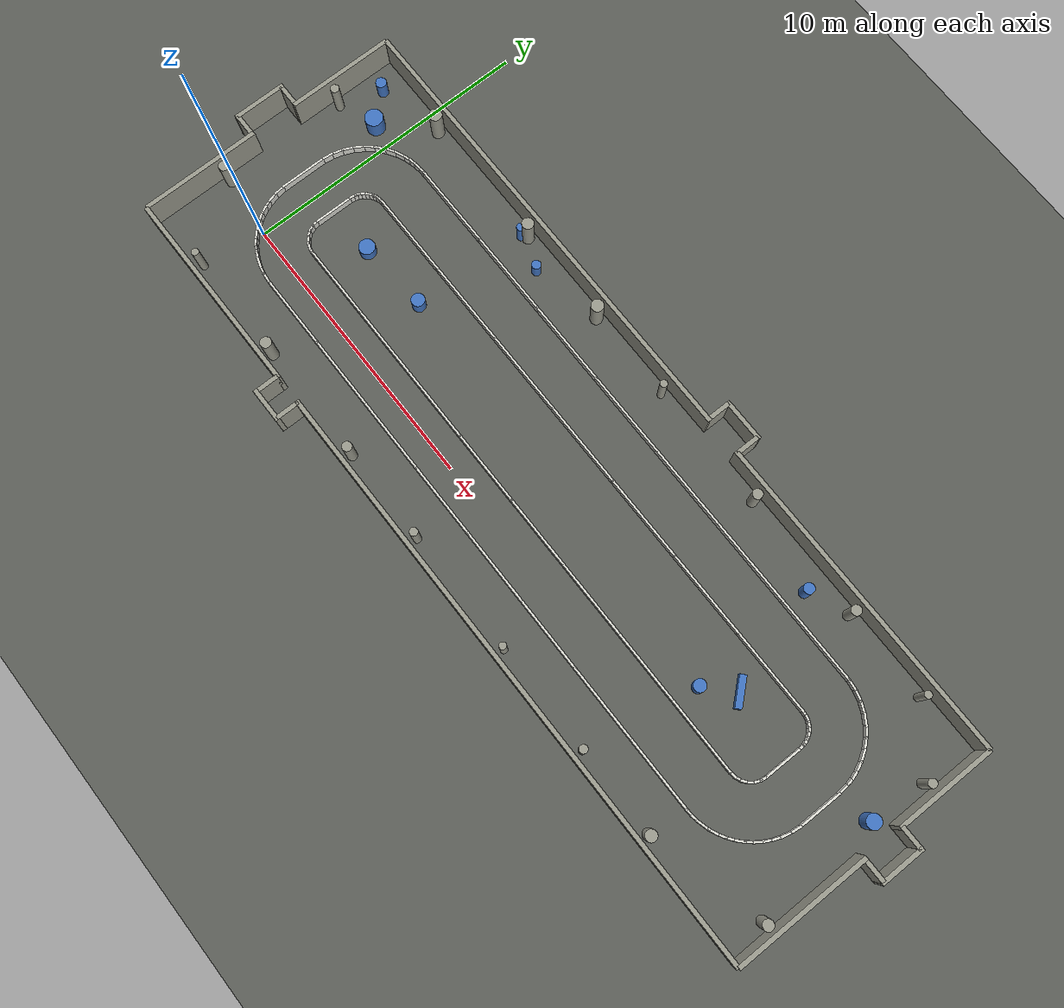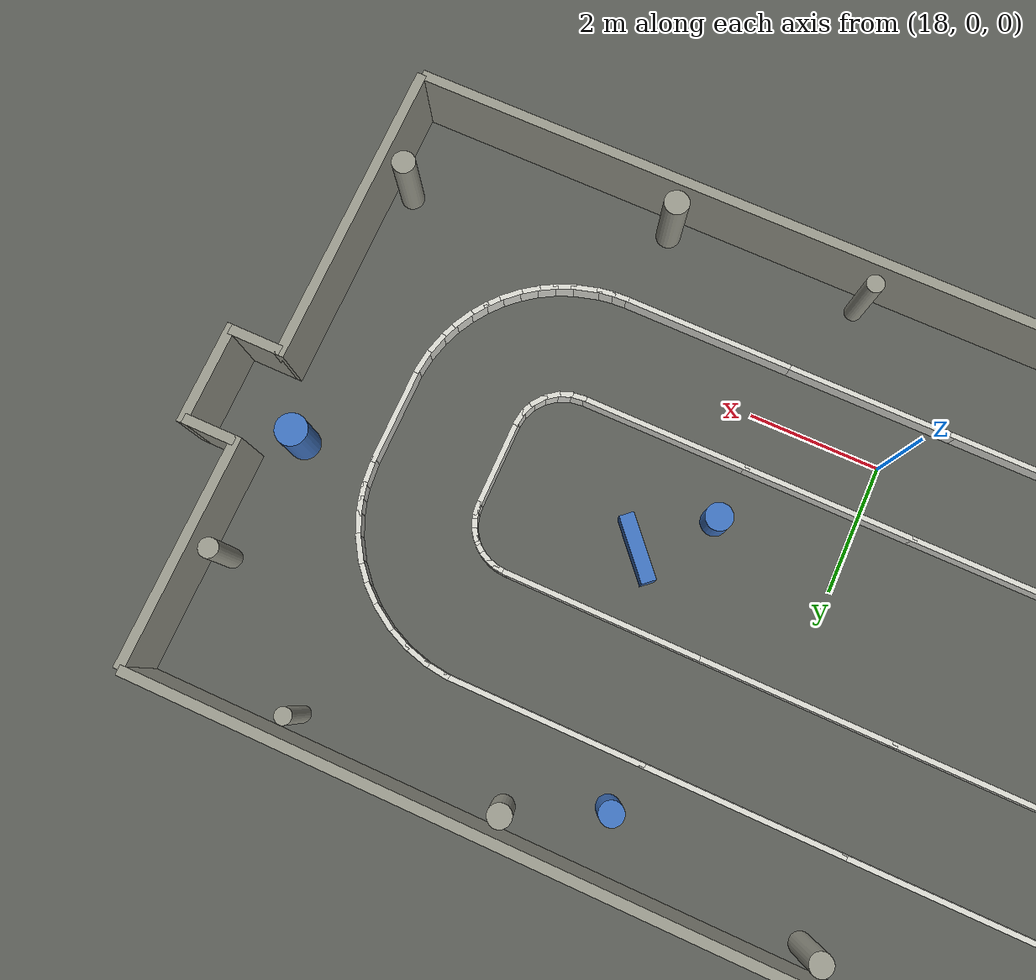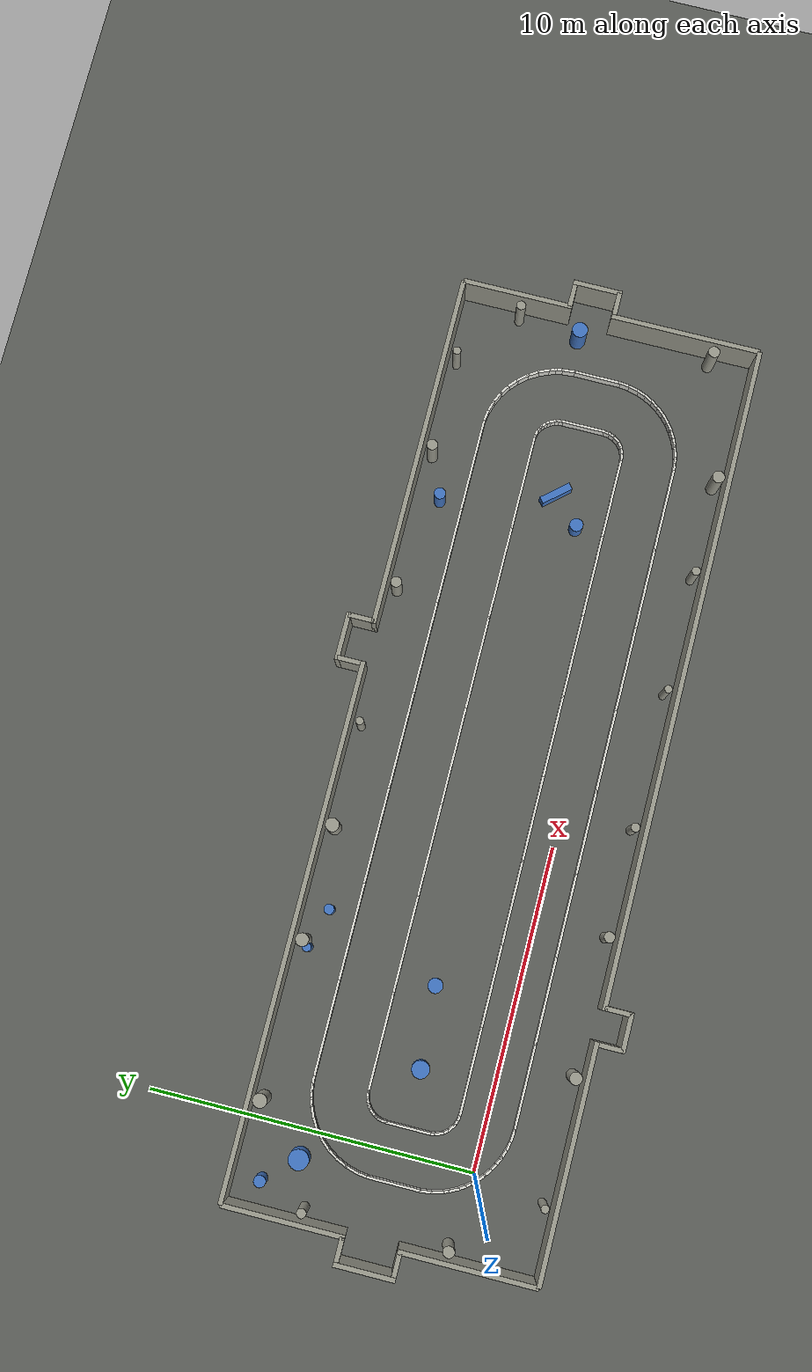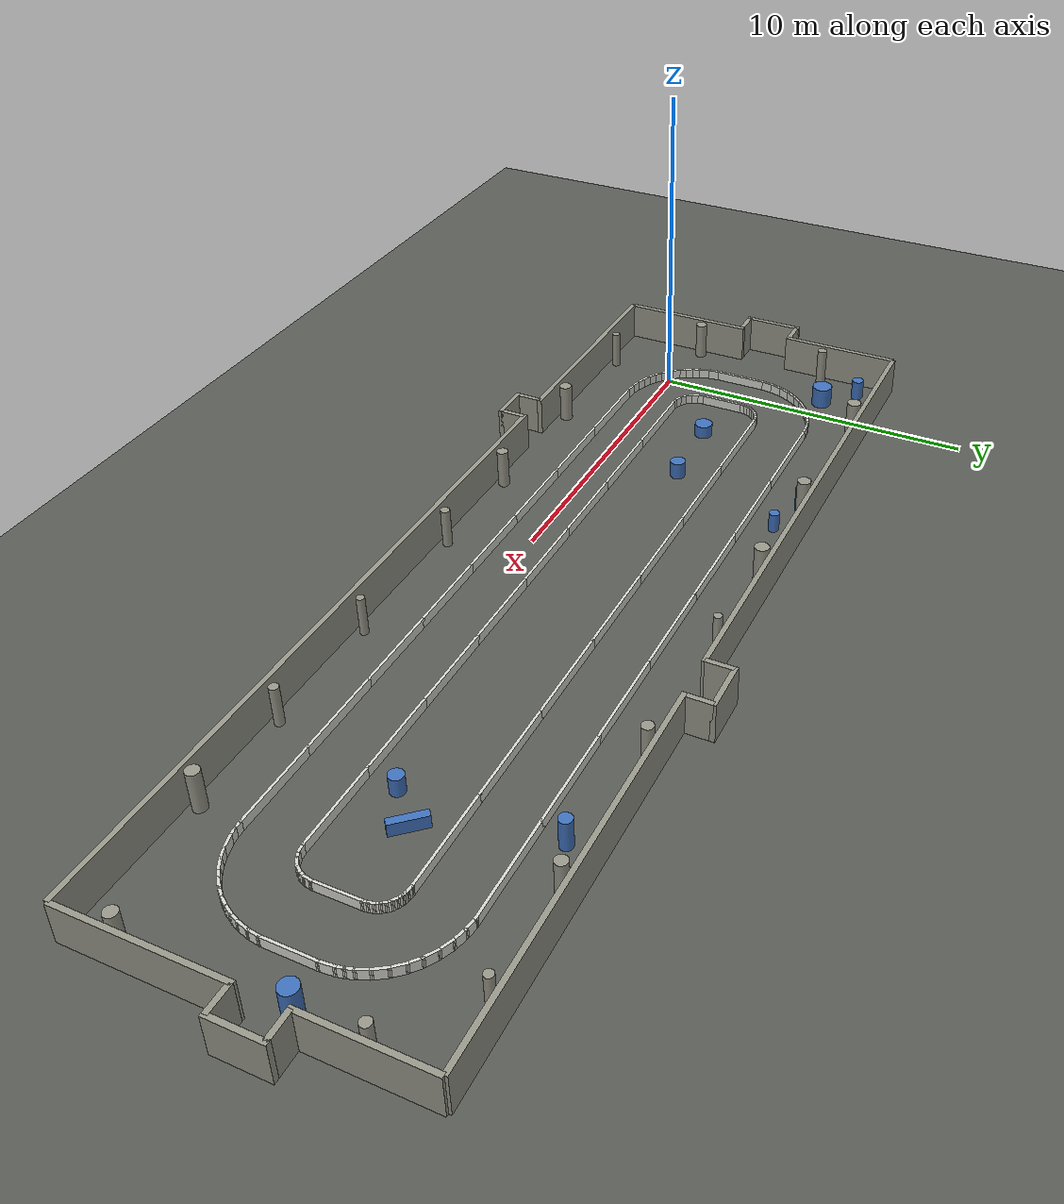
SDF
<?xml version="1.0" ?>
<sdf version="1.9">
  <!-- Generated by simulation/tools/generate_pose_dataset.py --install-gazebo-worlds from tools/pose_dataset/config/tracks.yaml (zs_warehouse_aisles). Do not edit by hand: change the YAML and regenerate. -->
  <world name="default">
    <physics name="default_physics" type="dart">
      <max_step_size>0.001</max_step_size>
      <real_time_factor>1.0</real_time_factor>
      <real_time_update_rate>1000.0</real_time_update_rate>
    </physics>
    <plugin filename="gz-sim-physics-system" name="gz::sim::systems::Physics" />
    <plugin filename="gz-sim-user-commands-system" name="gz::sim::systems::UserCommands" />
    <plugin filename="gz-sim-scene-broadcaster-system" name="gz::sim::systems::SceneBroadcaster" />
    <plugin filename="gz-sim-imu-system" name="gz::sim::systems::Imu" />
    <plugin filename="gz-sim-sensors-system" name="gz::sim::systems::Sensors">
      <render_engine>ogre2</render_engine>
    </plugin>
    <light type="directional" name="sun">
      <pose>0 0 10 0 0 0</pose>
      <diffuse>0.8 0.8 0.8 1</diffuse>
      <direction>-0.5 0.5 -1</direction>
      <cast_shadows>true</cast_shadows>
    </light>
    <model name="track_feature">
      <static>true</static>
      <pose>0 0 0 0 0 0</pose>
      <link name="feature_link">
        <collision name="feat_box_10_collision">
          <pose>20.805922 2.577946 0.189972 0.000000 0.000000 2.290240</pose>
          <geometry>
            <box>
              <size>1.032700 0.225423 0.379944</size>
            </box>
          </geometry>
        </collision>
        <visual name="feat_box_10_visual">
          <pose>20.805922 2.577946 0.189972 0.000000 0.000000 2.290240</pose>
          <geometry>
            <box>
              <size>1.032700 0.225423 0.379944</size>
            </box>
          </geometry>
          <material>
            <ambient>0.25 0.45 0.75 1</ambient>
            <diffuse>0.25 0.45 0.75 1</diffuse>
          </material>
        </visual>
        <collision name="feat_cyl_1_collision">
          <pose>5.095583 2.484080 0.261773 0.000000 0.000000 0.000000</pose>
          <geometry>
            <cylinder>
              <radius>0.228690</radius>
              <length>0.523547</length>
            </cylinder>
          </geometry>
        </collision>
        <visual name="feat_cyl_1_visual">
          <pose>5.095583 2.484080 0.261773 0.000000 0.000000 0.000000</pose>
          <geometry>
            <cylinder>
              <radius>0.228690</radius>
              <length>0.523547</length>
            </cylinder>
          </geometry>
          <material>
            <ambient>0.25 0.45 0.75 1</ambient>
            <diffuse>0.25 0.45 0.75 1</diffuse>
          </material>
        </visual>
        <collision name="feat_cyl_2_collision">
          <pose>19.747150 6.061025 0.442172 0.000000 0.000000 0.000000</pose>
          <geometry>
            <cylinder>
              <radius>0.181366</radius>
              <length>0.884344</length>
            </cylinder>
          </geometry>
        </collision>
        <visual name="feat_cyl_2_visual">
          <pose>19.747150 6.061025 0.442172 0.000000 0.000000 0.000000</pose>
          <geometry>
            <cylinder>
              <radius>0.181366</radius>
              <length>0.884344</length>
            </cylinder>
          </geometry>
          <material>
            <ambient>0.25 0.45 0.75 1</ambient>
            <diffuse>0.25 0.45 0.75 1</diffuse>
          </material>
        </visual>
        <collision name="feat_cyl_3_collision">
          <pose>19.917322 1.719447 0.268425 0.000000 0.000000 0.000000</pose>
          <geometry>
            <cylinder>
              <radius>0.210090</radius>
              <length>0.536850</length>
            </cylinder>
          </geometry>
        </collision>
        <visual name="feat_cyl_3_visual">
          <pose>19.917322 1.719447 0.268425 0.000000 0.000000 0.000000</pose>
          <geometry>
            <cylinder>
              <radius>0.210090</radius>
              <length>0.536850</length>
            </cylinder>
          </geometry>
          <material>
            <ambient>0.25 0.45 0.75 1</ambient>
            <diffuse>0.25 0.45 0.75 1</diffuse>
          </material>
        </visual>
        <collision name="feat_cyl_4_collision">
          <pose>-0.795670 5.149357 0.332980 0.000000 0.000000 0.000000</pose>
          <geometry>
            <cylinder>
              <radius>0.311442</radius>
              <length>0.665961</length>
            </cylinder>
          </geometry>
        </collision>
        <visual name="feat_cyl_4_visual">
          <pose>-0.795670 5.149357 0.332980 0.000000 0.000000 0.000000</pose>
          <geometry>
            <cylinder>
              <radius>0.311442</radius>
              <length>0.665961</length>
            </cylinder>
          </geometry>
          <material>
            <ambient>0.25 0.45 0.75 1</ambient>
            <diffuse>0.25 0.45 0.75 1</diffuse>
          </material>
        </visual>
        <collision name="feat_cyl_5_collision">
          <pose>6.516177 6.145721 0.294733 0.000000 0.000000 0.000000</pose>
          <geometry>
            <cylinder>
              <radius>0.156200</radius>
              <length>0.589467</length>
            </cylinder>
          </geometry>
        </collision>
        <visual name="feat_cyl_5_visual">
          <pose>6.516177 6.145721 0.294733 0.000000 0.000000 0.000000</pose>
          <geometry>
            <cylinder>
              <radius>0.156200</radius>
              <length>0.589467</length>
            </cylinder>
          </geometry>
          <material>
            <ambient>0.25 0.45 0.75 1</ambient>
            <diffuse>0.25 0.45 0.75 1</diffuse>
          </material>
        </visual>
        <collision name="feat_cyl_6_collision">
          <pose>2.591725 2.308717 0.205123 0.000000 0.000000 0.000000</pose>
          <geometry>
            <cylinder>
              <radius>0.275531</radius>
              <length>0.410247</length>
            </cylinder>
          </geometry>
        </collision>
        <visual name="feat_cyl_6_visual">
          <pose>2.591725 2.308717 0.205123 0.000000 0.000000 0.000000</pose>
          <geometry>
            <cylinder>
              <radius>0.275531</radius>
              <length>0.410247</length>
            </cylinder>
          </geometry>
          <material>
            <ambient>0.25 0.45 0.75 1</ambient>
            <diffuse>0.25 0.45 0.75 1</diffuse>
          </material>
        </visual>
        <collision name="feat_cyl_7_collision">
          <pose>25.949225 3.094233 0.459818 0.000000 0.000000 0.000000</pose>
          <geometry>
            <cylinder>
              <radius>0.244701</radius>
              <length>0.919635</length>
            </cylinder>
          </geometry>
        </collision>
        <visual name="feat_cyl_7_visual">
          <pose>25.949225 3.094233 0.459818 0.000000 0.000000 0.000000</pose>
          <geometry>
            <cylinder>
              <radius>0.244701</radius>
              <length>0.919635</length>
            </cylinder>
          </geometry>
          <material>
            <ambient>0.25 0.45 0.75 1</ambient>
            <diffuse>0.25 0.45 0.75 1</diffuse>
          </material>
        </visual>
        <collision name="feat_cyl_8_collision">
          <pose>-1.677320 6.098490 0.323803 0.000000 0.000000 0.000000</pose>
          <geometry>
            <cylinder>
              <radius>0.183685</radius>
              <length>0.647605</length>
            </cylinder>
          </geometry>
        </collision>
        <visual name="feat_cyl_8_visual">
          <pose>-1.677320 6.098490 0.323803 0.000000 0.000000 0.000000</pose>
          <geometry>
            <cylinder>
              <radius>0.183685</radius>
              <length>0.647605</length>
            </cylinder>
          </geometry>
          <material>
            <ambient>0.25 0.45 0.75 1</ambient>
            <diffuse>0.25 0.45 0.75 1</diffuse>
          </material>
        </visual>
        <collision name="feat_cyl_9_collision">
          <pose>5.265680 6.496710 0.399092 0.000000 0.000000 0.000000</pose>
          <geometry>
            <cylinder>
              <radius>0.138124</radius>
              <length>0.798185</length>
            </cylinder>
          </geometry>
        </collision>
        <visual name="feat_cyl_9_visual">
          <pose>5.265680 6.496710 0.399092 0.000000 0.000000 0.000000</pose>
          <geometry>
            <cylinder>
              <radius>0.138124</radius>
              <length>0.798185</length>
            </cylinder>
          </geometry>
          <material>
            <ambient>0.25 0.45 0.75 1</ambient>
            <diffuse>0.25 0.45 0.75 1</diffuse>
          </material>
        </visual>
      </link>
    </model>
    <model name="track_ground">
      <static>true</static>
      <pose>0 0 0 0 0 0</pose>
      <link name="ground_link">
        <collision name="ground_collision">
          <pose>12.000000 2.250000 -0.025000 0.000000 0.000000 0.000000</pose>
          <geometry>
            <box>
              <size>80.000000 80.000000 0.050000</size>
            </box>
          </geometry>
          <surface>
            <friction>
              <ode>
                <mu>1.2</mu>
                <mu2>1.2</mu2>
              </ode>
            </friction>
            <contact>
              <ode>
                <kp>100000.0</kp>
                <kd>10.0</kd>
              </ode>
            </contact>
          </surface>
        </collision>
        <visual name="ground_visual">
          <pose>12.000000 2.250000 -0.025000 0.000000 0.000000 0.000000</pose>
          <geometry>
            <box>
              <size>80.000000 80.000000 0.050000</size>
            </box>
          </geometry>
          <material>
            <ambient>0.35 0.36 0.34 1</ambient>
            <diffuse>0.35 0.36 0.34 1</diffuse>
          </material>
        </visual>
      </link>
    </model>
    <model name="track_room">
      <static>true</static>
      <pose>0 0 0 0 0 0</pose>
      <link name="room_link">
        <collision name="hall_0_0_collision">
          <pose>1.104349 -2.500000 0.600000 0.000000 0.000000 0.000000</pose>
          <geometry>
            <box>
              <size>7.208698 0.150000 1.200000</size>
            </box>
          </geometry>
        </collision>
        <visual name="hall_0_0_visual">
          <pose>1.104349 -2.500000 0.600000 0.000000 0.000000 0.000000</pose>
          <geometry>
            <box>
              <size>7.208698 0.150000 1.200000</size>
            </box>
          </geometry>
          <material>
            <ambient>0.6 0.6 0.55 1</ambient>
            <diffuse>0.6 0.6 0.55 1</diffuse>
          </material>
        </visual>
        <collision name="hall_0_81_collision">
          <pose>16.066658 -2.500000 0.600000 0.000000 0.000000 0.000000</pose>
          <geometry>
            <box>
              <size>20.866685 0.150000 1.200000</size>
            </box>
          </geometry>
        </collision>
        <visual name="hall_0_81_visual">
          <pose>16.066658 -2.500000 0.600000 0.000000 0.000000 0.000000</pose>
          <geometry>
            <box>
              <size>20.866685 0.150000 1.200000</size>
            </box>
          </geometry>
          <material>
            <ambient>0.6 0.6 0.55 1</ambient>
            <diffuse>0.6 0.6 0.55 1</diffuse>
          </material>
        </visual>
        <collision name="hall_niche_0_collision">
          <pose>5.171007 -3.300000 0.600000 0.000000 0.000000 0.000000</pose>
          <geometry>
            <box>
              <size>1.224618 0.150000 1.200000</size>
            </box>
          </geometry>
        </collision>
        <visual name="hall_niche_0_visual">
          <pose>5.171007 -3.300000 0.600000 0.000000 0.000000 0.000000</pose>
          <geometry>
            <box>
              <size>1.224618 0.150000 1.200000</size>
            </box>
          </geometry>
          <material>
            <ambient>0.6 0.6 0.55 1</ambient>
            <diffuse>0.6 0.6 0.55 1</diffuse>
          </material>
        </visual>
        <collision name="hall_jamb_0_-1_collision">
          <pose>4.633698 -2.900000 0.600000 0.000000 0.000000 0.000000</pose>
          <geometry>
            <box>
              <size>0.150000 0.800000 1.200000</size>
            </box>
          </geometry>
        </collision>
        <visual name="hall_jamb_0_-1_visual">
          <pose>4.633698 -2.900000 0.600000 0.000000 0.000000 0.000000</pose>
          <geometry>
            <box>
              <size>0.150000 0.800000 1.200000</size>
            </box>
          </geometry>
          <material>
            <ambient>0.6 0.6 0.55 1</ambient>
            <diffuse>0.6 0.6 0.55 1</diffuse>
          </material>
        </visual>
        <collision name="hall_jamb_0_1_collision">
          <pose>5.708315 -2.900000 0.600000 0.000000 0.000000 0.000000</pose>
          <geometry>
            <box>
              <size>0.150000 0.800000 1.200000</size>
            </box>
          </geometry>
        </collision>
        <visual name="hall_jamb_0_1_visual">
          <pose>5.708315 -2.900000 0.600000 0.000000 0.000000 0.000000</pose>
          <geometry>
            <box>
              <size>0.150000 0.800000 1.200000</size>
            </box>
          </geometry>
          <material>
            <ambient>0.6 0.6 0.55 1</ambient>
            <diffuse>0.6 0.6 0.55 1</diffuse>
          </material>
        </visual>
        <collision name="hall_1_0_collision">
          <pose>26.500000 -0.127356 0.600000 0.000000 0.000000 1.570796</pose>
          <geometry>
            <box>
              <size>4.745288 0.150000 1.200000</size>
            </box>
          </geometry>
        </collision>
        <visual name="hall_1_0_visual">
          <pose>26.500000 -0.127356 0.600000 0.000000 0.000000 1.570796</pose>
          <geometry>
            <box>
              <size>4.745288 0.150000 1.200000</size>
            </box>
          </geometry>
          <material>
            <ambient>0.6 0.6 0.55 1</ambient>
            <diffuse>0.6 0.6 0.55 1</diffuse>
          </material>
        </visual>
        <collision name="hall_1_60_collision">
          <pose>26.500000 5.256696 0.600000 0.000000 0.000000 1.570796</pose>
          <geometry>
            <box>
              <size>3.486608 0.150000 1.200000</size>
            </box>
          </geometry>
        </collision>
        <visual name="hall_1_60_visual">
          <pose>26.500000 5.256696 0.600000 0.000000 0.000000 1.570796</pose>
          <geometry>
            <box>
              <size>3.486608 0.150000 1.200000</size>
            </box>
          </geometry>
          <material>
            <ambient>0.6 0.6 0.55 1</ambient>
            <diffuse>0.6 0.6 0.55 1</diffuse>
          </material>
        </visual>
        <collision name="hall_niche_1_collision">
          <pose>27.300000 2.879340 0.600000 0.000000 0.000000 1.570796</pose>
          <geometry>
            <box>
              <size>1.568104 0.150000 1.200000</size>
            </box>
          </geometry>
        </collision>
        <visual name="hall_niche_1_visual">
          <pose>27.300000 2.879340 0.600000 0.000000 0.000000 1.570796</pose>
          <geometry>
            <box>
              <size>1.568104 0.150000 1.200000</size>
            </box>
          </geometry>
          <material>
            <ambient>0.6 0.6 0.55 1</ambient>
            <diffuse>0.6 0.6 0.55 1</diffuse>
          </material>
        </visual>
        <collision name="hall_jamb_1_-1_collision">
          <pose>26.900000 2.170288 0.600000 0.000000 0.000000 1.570796</pose>
          <geometry>
            <box>
              <size>0.150000 0.800000 1.200000</size>
            </box>
          </geometry>
        </collision>
        <visual name="hall_jamb_1_-1_visual">
          <pose>26.900000 2.170288 0.600000 0.000000 0.000000 1.570796</pose>
          <geometry>
            <box>
              <size>0.150000 0.800000 1.200000</size>
            </box>
          </geometry>
          <material>
            <ambient>0.6 0.6 0.55 1</ambient>
            <diffuse>0.6 0.6 0.55 1</diffuse>
          </material>
        </visual>
        <collision name="hall_jamb_1_1_collision">
          <pose>26.900000 3.588392 0.600000 0.000000 0.000000 1.570796</pose>
          <geometry>
            <box>
              <size>0.150000 0.800000 1.200000</size>
            </box>
          </geometry>
        </collision>
        <visual name="hall_jamb_1_1_visual">
          <pose>26.900000 3.588392 0.600000 0.000000 0.000000 1.570796</pose>
          <geometry>
            <box>
              <size>0.150000 0.800000 1.200000</size>
            </box>
          </geometry>
          <material>
            <ambient>0.6 0.6 0.55 1</ambient>
            <diffuse>0.6 0.6 0.55 1</diffuse>
          </material>
        </visual>
        <collision name="hall_2_0_collision">
          <pose>20.854480 7.000000 0.600000 0.000000 0.000000 3.141593</pose>
          <geometry>
            <box>
              <size>11.291040 0.150000 1.200000</size>
            </box>
          </geometry>
        </collision>
        <visual name="hall_2_0_visual">
          <pose>20.854480 7.000000 0.600000 0.000000 0.000000 3.141593</pose>
          <geometry>
            <box>
              <size>11.291040 0.150000 1.200000</size>
            </box>
          </geometry>
          <material>
            <ambient>0.6 0.6 0.55 1</ambient>
            <diffuse>0.6 0.6 0.55 1</diffuse>
          </material>
        </visual>
        <collision name="hall_2_125_collision">
          <pose>5.748405 7.000000 0.600000 0.000000 0.000000 3.141593</pose>
          <geometry>
            <box>
              <size>16.496811 0.150000 1.200000</size>
            </box>
          </geometry>
        </collision>
        <visual name="hall_2_125_visual">
          <pose>5.748405 7.000000 0.600000 0.000000 0.000000 3.141593</pose>
          <geometry>
            <box>
              <size>16.496811 0.150000 1.200000</size>
            </box>
          </geometry>
          <material>
            <ambient>0.6 0.6 0.55 1</ambient>
            <diffuse>0.6 0.6 0.55 1</diffuse>
          </material>
        </visual>
        <collision name="hall_niche_2_collision">
          <pose>14.602885 7.800000 0.600000 0.000000 0.000000 3.141593</pose>
          <geometry>
            <box>
              <size>1.512149 0.150000 1.200000</size>
            </box>
          </geometry>
        </collision>
        <visual name="hall_niche_2_visual">
          <pose>14.602885 7.800000 0.600000 0.000000 0.000000 3.141593</pose>
          <geometry>
            <box>
              <size>1.512149 0.150000 1.200000</size>
            </box>
          </geometry>
          <material>
            <ambient>0.6 0.6 0.55 1</ambient>
            <diffuse>0.6 0.6 0.55 1</diffuse>
          </material>
        </visual>
        <collision name="hall_jamb_2_-1_collision">
          <pose>15.283960 7.400000 0.600000 0.000000 0.000000 3.141593</pose>
          <geometry>
            <box>
              <size>0.150000 0.800000 1.200000</size>
            </box>
          </geometry>
        </collision>
        <visual name="hall_jamb_2_-1_visual">
          <pose>15.283960 7.400000 0.600000 0.000000 0.000000 3.141593</pose>
          <geometry>
            <box>
              <size>0.150000 0.800000 1.200000</size>
            </box>
          </geometry>
          <material>
            <ambient>0.6 0.6 0.55 1</ambient>
            <diffuse>0.6 0.6 0.55 1</diffuse>
          </material>
        </visual>
        <collision name="hall_jamb_2_1_collision">
          <pose>13.921811 7.400000 0.600000 0.000000 0.000000 3.141593</pose>
          <geometry>
            <box>
              <size>0.150000 0.800000 1.200000</size>
            </box>
          </geometry>
        </collision>
        <visual name="hall_jamb_2_1_visual">
          <pose>13.921811 7.400000 0.600000 0.000000 0.000000 3.141593</pose>
          <geometry>
            <box>
              <size>0.150000 0.800000 1.200000</size>
            </box>
          </geometry>
          <material>
            <ambient>0.6 0.6 0.55 1</ambient>
            <diffuse>0.6 0.6 0.55 1</diffuse>
          </material>
        </visual>
        <collision name="hall_3_0_collision">
          <pose>-2.500000 5.130584 0.600000 0.000000 0.000000 -1.570796</pose>
          <geometry>
            <box>
              <size>3.738832 0.150000 1.200000</size>
            </box>
          </geometry>
        </collision>
        <visual name="hall_3_0_visual">
          <pose>-2.500000 5.130584 0.600000 0.000000 0.000000 -1.570796</pose>
          <geometry>
            <box>
              <size>3.738832 0.150000 1.200000</size>
            </box>
          </geometry>
          <material>
            <ambient>0.6 0.6 0.55 1</ambient>
            <diffuse>0.6 0.6 0.55 1</diffuse>
          </material>
        </visual>
        <collision name="hall_3_53_collision">
          <pose>-2.500000 -0.402749 0.600000 0.000000 0.000000 -1.570796</pose>
          <geometry>
            <box>
              <size>4.194502 0.150000 1.200000</size>
            </box>
          </geometry>
        </collision>
        <visual name="hall_3_53_visual">
          <pose>-2.500000 -0.402749 0.600000 0.000000 0.000000 -1.570796</pose>
          <geometry>
            <box>
              <size>4.194502 0.150000 1.200000</size>
            </box>
          </geometry>
          <material>
            <ambient>0.6 0.6 0.55 1</ambient>
            <diffuse>0.6 0.6 0.55 1</diffuse>
          </material>
        </visual>
        <collision name="hall_niche_3_collision">
          <pose>-3.300000 2.477835 0.600000 0.000000 0.000000 -1.570796</pose>
          <geometry>
            <box>
              <size>1.866666 0.150000 1.200000</size>
            </box>
          </geometry>
        </collision>
        <visual name="hall_niche_3_visual">
          <pose>-3.300000 2.477835 0.600000 0.000000 0.000000 -1.570796</pose>
          <geometry>
            <box>
              <size>1.866666 0.150000 1.200000</size>
            </box>
          </geometry>
          <material>
            <ambient>0.6 0.6 0.55 1</ambient>
            <diffuse>0.6 0.6 0.55 1</diffuse>
          </material>
        </visual>
        <collision name="hall_jamb_3_-1_collision">
          <pose>-2.900000 3.336168 0.600000 0.000000 0.000000 -1.570796</pose>
          <geometry>
            <box>
              <size>0.150000 0.800000 1.200000</size>
            </box>
          </geometry>
        </collision>
        <visual name="hall_jamb_3_-1_visual">
          <pose>-2.900000 3.336168 0.600000 0.000000 0.000000 -1.570796</pose>
          <geometry>
            <box>
              <size>0.150000 0.800000 1.200000</size>
            </box>
          </geometry>
          <material>
            <ambient>0.6 0.6 0.55 1</ambient>
            <diffuse>0.6 0.6 0.55 1</diffuse>
          </material>
        </visual>
        <collision name="hall_jamb_3_1_collision">
          <pose>-2.900000 1.619502 0.600000 0.000000 0.000000 -1.570796</pose>
          <geometry>
            <box>
              <size>0.150000 0.800000 1.200000</size>
            </box>
          </geometry>
        </collision>
        <visual name="hall_jamb_3_1_visual">
          <pose>-2.900000 1.619502 0.600000 0.000000 0.000000 -1.570796</pose>
          <geometry>
            <box>
              <size>0.150000 0.800000 1.200000</size>
            </box>
          </geometry>
          <material>
            <ambient>0.6 0.6 0.55 1</ambient>
            <diffuse>0.6 0.6 0.55 1</diffuse>
          </material>
        </visual>
        <collision name="column_0_22_collision">
          <pose>-0.297476 -2.150000 0.600000 0.000000 0.000000 0.000000</pose>
          <geometry>
            <cylinder>
              <radius>0.125315</radius>
              <length>1.200000</length>
            </cylinder>
          </geometry>
        </collision>
        <visual name="column_0_22_visual">
          <pose>-0.297476 -2.150000 0.600000 0.000000 0.000000 0.000000</pose>
          <geometry>
            <cylinder>
              <radius>0.125315</radius>
              <length>1.200000</length>
            </cylinder>
          </geometry>
          <material>
            <ambient>0.6 0.6 0.55 1</ambient>
            <diffuse>0.6 0.6 0.55 1</diffuse>
          </material>
        </visual>
        <collision name="column_0_60_collision">
          <pose>3.524388 -2.150000 0.600000 0.000000 0.000000 0.000000</pose>
          <geometry>
            <cylinder>
              <radius>0.190937</radius>
              <length>1.200000</length>
            </cylinder>
          </geometry>
        </collision>
        <visual name="column_0_60_visual">
          <pose>3.524388 -2.150000 0.600000 0.000000 0.000000 0.000000</pose>
          <geometry>
            <cylinder>
              <radius>0.190937</radius>
              <length>1.200000</length>
            </cylinder>
          </geometry>
          <material>
            <ambient>0.6 0.6 0.55 1</ambient>
            <diffuse>0.6 0.6 0.55 1</diffuse>
          </material>
        </visual>
        <collision name="column_0_102_collision">
          <pose>7.755703 -2.150000 0.600000 0.000000 0.000000 0.000000</pose>
          <geometry>
            <cylinder>
              <radius>0.166855</radius>
              <length>1.200000</length>
            </cylinder>
          </geometry>
        </collision>
        <visual name="column_0_102_visual">
          <pose>7.755703 -2.150000 0.600000 0.000000 0.000000 0.000000</pose>
          <geometry>
            <cylinder>
              <radius>0.166855</radius>
              <length>1.200000</length>
            </cylinder>
          </geometry>
          <material>
            <ambient>0.6 0.6 0.55 1</ambient>
            <diffuse>0.6 0.6 0.55 1</diffuse>
          </material>
        </visual>
        <collision name="column_0_136_collision">
          <pose>11.115146 -2.150000 0.600000 0.000000 0.000000 0.000000</pose>
          <geometry>
            <cylinder>
              <radius>0.138892</radius>
              <length>1.200000</length>
            </cylinder>
          </geometry>
        </collision>
        <visual name="column_0_136_visual">
          <pose>11.115146 -2.150000 0.600000 0.000000 0.000000 0.000000</pose>
          <geometry>
            <cylinder>
              <radius>0.138892</radius>
              <length>1.200000</length>
            </cylinder>
          </geometry>
          <material>
            <ambient>0.6 0.6 0.55 1</ambient>
            <diffuse>0.6 0.6 0.55 1</diffuse>
          </material>
        </visual>
        <collision name="column_0_179_collision">
          <pose>15.438039 -2.150000 0.600000 0.000000 0.000000 0.000000</pose>
          <geometry>
            <cylinder>
              <radius>0.120638</radius>
              <length>1.200000</length>
            </cylinder>
          </geometry>
        </collision>
        <visual name="column_0_179_visual">
          <pose>15.438039 -2.150000 0.600000 0.000000 0.000000 0.000000</pose>
          <geometry>
            <cylinder>
              <radius>0.120638</radius>
              <length>1.200000</length>
            </cylinder>
          </geometry>
          <material>
            <ambient>0.6 0.6 0.55 1</ambient>
            <diffuse>0.6 0.6 0.55 1</diffuse>
          </material>
        </visual>
        <collision name="column_0_217_collision">
          <pose>19.205895 -2.150000 0.600000 0.000000 0.000000 0.000000</pose>
          <geometry>
            <cylinder>
              <radius>0.136682</radius>
              <length>1.200000</length>
            </cylinder>
          </geometry>
        </collision>
        <visual name="column_0_217_visual">
          <pose>19.205895 -2.150000 0.600000 0.000000 0.000000 0.000000</pose>
          <geometry>
            <cylinder>
              <radius>0.136682</radius>
              <length>1.200000</length>
            </cylinder>
          </geometry>
          <material>
            <ambient>0.6 0.6 0.55 1</ambient>
            <diffuse>0.6 0.6 0.55 1</diffuse>
          </material>
        </visual>
        <collision name="column_0_247_collision">
          <pose>22.267137 -2.150000 0.600000 0.000000 0.000000 0.000000</pose>
          <geometry>
            <cylinder>
              <radius>0.191714</radius>
              <length>1.200000</length>
            </cylinder>
          </geometry>
        </collision>
        <visual name="column_0_247_visual">
          <pose>22.267137 -2.150000 0.600000 0.000000 0.000000 0.000000</pose>
          <geometry>
            <cylinder>
              <radius>0.191714</radius>
              <length>1.200000</length>
            </cylinder>
          </geometry>
          <material>
            <ambient>0.6 0.6 0.55 1</ambient>
            <diffuse>0.6 0.6 0.55 1</diffuse>
          </material>
        </visual>
        <collision name="column_1_13_collision">
          <pose>26.150000 -1.119888 0.600000 0.000000 0.000000 0.000000</pose>
          <geometry>
            <cylinder>
              <radius>0.180215</radius>
              <length>1.200000</length>
            </cylinder>
          </geometry>
        </collision>
        <visual name="column_1_13_visual">
          <pose>26.150000 -1.119888 0.600000 0.000000 0.000000 0.000000</pose>
          <geometry>
            <cylinder>
              <radius>0.180215</radius>
              <length>1.200000</length>
            </cylinder>
          </geometry>
          <material>
            <ambient>0.6 0.6 0.55 1</ambient>
            <diffuse>0.6 0.6 0.55 1</diffuse>
          </material>
        </visual>
        <collision name="column_1_75_collision">
          <pose>26.150000 5.062594 0.600000 0.000000 0.000000 0.000000</pose>
          <geometry>
            <cylinder>
              <radius>0.147237</radius>
              <length>1.200000</length>
            </cylinder>
          </geometry>
        </collision>
        <visual name="column_1_75_visual">
          <pose>26.150000 5.062594 0.600000 0.000000 0.000000 0.000000</pose>
          <geometry>
            <cylinder>
              <radius>0.147237</radius>
              <length>1.200000</length>
            </cylinder>
          </geometry>
          <material>
            <ambient>0.6 0.6 0.55 1</ambient>
            <diffuse>0.6 0.6 0.55 1</diffuse>
          </material>
        </visual>
        <collision name="column_2_22_collision">
          <pose>24.224226 6.650000 0.600000 0.000000 0.000000 0.000000</pose>
          <geometry>
            <cylinder>
              <radius>0.124447</radius>
              <length>1.200000</length>
            </cylinder>
          </geometry>
        </collision>
        <visual name="column_2_22_visual">
          <pose>24.224226 6.650000 0.600000 0.000000 0.000000 0.000000</pose>
          <geometry>
            <cylinder>
              <radius>0.124447</radius>
              <length>1.200000</length>
            </cylinder>
          </geometry>
          <material>
            <ambient>0.6 0.6 0.55 1</ambient>
            <diffuse>0.6 0.6 0.55 1</diffuse>
          </material>
        </visual>
        <collision name="column_2_54_collision">
          <pose>21.094903 6.650000 0.600000 0.000000 0.000000 0.000000</pose>
          <geometry>
            <cylinder>
              <radius>0.172333</radius>
              <length>1.200000</length>
            </cylinder>
          </geometry>
        </collision>
        <visual name="column_2_54_visual">
          <pose>21.094903 6.650000 0.600000 0.000000 0.000000 0.000000</pose>
          <geometry>
            <cylinder>
              <radius>0.172333</radius>
              <length>1.200000</length>
            </cylinder>
          </geometry>
          <material>
            <ambient>0.6 0.6 0.55 1</ambient>
            <diffuse>0.6 0.6 0.55 1</diffuse>
          </material>
        </visual>
        <collision name="column_2_98_collision">
          <pose>16.626565 6.650000 0.600000 0.000000 0.000000 0.000000</pose>
          <geometry>
            <cylinder>
              <radius>0.169479</radius>
              <length>1.200000</length>
            </cylinder>
          </geometry>
        </collision>
        <visual name="column_2_98_visual">
          <pose>16.626565 6.650000 0.600000 0.000000 0.000000 0.000000</pose>
          <geometry>
            <cylinder>
              <radius>0.169479</radius>
              <length>1.200000</length>
            </cylinder>
          </geometry>
          <material>
            <ambient>0.6 0.6 0.55 1</ambient>
            <diffuse>0.6 0.6 0.55 1</diffuse>
          </material>
        </visual>
        <collision name="column_2_142_collision">
          <pose>12.201430 6.650000 0.600000 0.000000 0.000000 0.000000</pose>
          <geometry>
            <cylinder>
              <radius>0.123446</radius>
              <length>1.200000</length>
            </cylinder>
          </geometry>
        </collision>
        <visual name="column_2_142_visual">
          <pose>12.201430 6.650000 0.600000 0.000000 0.000000 0.000000</pose>
          <geometry>
            <cylinder>
              <radius>0.123446</radius>
              <length>1.200000</length>
            </cylinder>
          </geometry>
          <material>
            <ambient>0.6 0.6 0.55 1</ambient>
            <diffuse>0.6 0.6 0.55 1</diffuse>
          </material>
        </visual>
        <collision name="column_2_175_collision">
          <pose>8.965460 6.650000 0.600000 0.000000 0.000000 0.000000</pose>
          <geometry>
            <cylinder>
              <radius>0.213693</radius>
              <length>1.200000</length>
            </cylinder>
          </geometry>
        </collision>
        <visual name="column_2_175_visual">
          <pose>8.965460 6.650000 0.600000 0.000000 0.000000 0.000000</pose>
          <geometry>
            <cylinder>
              <radius>0.213693</radius>
              <length>1.200000</length>
            </cylinder>
          </geometry>
          <material>
            <ambient>0.6 0.6 0.55 1</ambient>
            <diffuse>0.6 0.6 0.55 1</diffuse>
          </material>
        </visual>
        <collision name="column_2_210_collision">
          <pose>5.453627 6.650000 0.600000 0.000000 0.000000 0.000000</pose>
          <geometry>
            <cylinder>
              <radius>0.202166</radius>
              <length>1.200000</length>
            </cylinder>
          </geometry>
        </collision>
        <visual name="column_2_210_visual">
          <pose>5.453627 6.650000 0.600000 0.000000 0.000000 0.000000</pose>
          <geometry>
            <cylinder>
              <radius>0.202166</radius>
              <length>1.200000</length>
            </cylinder>
          </geometry>
          <material>
            <ambient>0.6 0.6 0.55 1</ambient>
            <diffuse>0.6 0.6 0.55 1</diffuse>
          </material>
        </visual>
        <collision name="column_2_258_collision">
          <pose>0.636371 6.650000 0.600000 0.000000 0.000000 0.000000</pose>
          <geometry>
            <cylinder>
              <radius>0.217454</radius>
              <length>1.200000</length>
            </cylinder>
          </geometry>
        </collision>
        <visual name="column_2_258_visual">
          <pose>0.636371 6.650000 0.600000 0.000000 0.000000 0.000000</pose>
          <geometry>
            <cylinder>
              <radius>0.217454</radius>
              <length>1.200000</length>
            </cylinder>
          </geometry>
          <material>
            <ambient>0.6 0.6 0.55 1</ambient>
            <diffuse>0.6 0.6 0.55 1</diffuse>
          </material>
        </visual>
        <collision name="column_3_23_collision">
          <pose>-2.150000 4.655249 0.600000 0.000000 0.000000 0.000000</pose>
          <geometry>
            <cylinder>
              <radius>0.147045</radius>
              <length>1.200000</length>
            </cylinder>
          </geometry>
        </collision>
        <visual name="column_3_23_visual">
          <pose>-2.150000 4.655249 0.600000 0.000000 0.000000 0.000000</pose>
          <geometry>
            <cylinder>
              <radius>0.147045</radius>
              <length>1.200000</length>
            </cylinder>
          </geometry>
          <material>
            <ambient>0.6 0.6 0.55 1</ambient>
            <diffuse>0.6 0.6 0.55 1</diffuse>
          </material>
        </visual>
        <collision name="column_3_67_collision">
          <pose>-2.150000 0.257397 0.600000 0.000000 0.000000 0.000000</pose>
          <geometry>
            <cylinder>
              <radius>0.178024</radius>
              <length>1.200000</length>
            </cylinder>
          </geometry>
        </collision>
        <visual name="column_3_67_visual">
          <pose>-2.150000 0.257397 0.600000 0.000000 0.000000 0.000000</pose>
          <geometry>
            <cylinder>
              <radius>0.178024</radius>
              <length>1.200000</length>
            </cylinder>
          </geometry>
          <material>
            <ambient>0.6 0.6 0.55 1</ambient>
            <diffuse>0.6 0.6 0.55 1</diffuse>
          </material>
        </visual>
      </link>
    </model>
    <model name="track_wall">
      <static>true</static>
      <pose>0 0 0 0 0 0</pose>
      <link name="wall_link">
        <collision name="left0_0_0_collision">
          <pose>13.299673 0.839999 0.150000 0.000000 0.000000 -0.000000</pose>
          <geometry>
            <box>
              <size>2.679346 0.080000 0.300000</size>
            </box>
          </geometry>
        </collision>
        <visual name="left0_0_0_visual">
          <pose>13.299673 0.839999 0.150000 0.000000 0.000000 -0.000000</pose>
          <geometry>
            <box>
              <size>2.679346 0.080000 0.300000</size>
            </box>
          </geometry>
          <material>
            <ambient>0.85 0.85 0.82 1</ambient>
            <diffuse>0.85 0.85 0.82 1</diffuse>
          </material>
        </visual>
        <collision name="left0_0_1_collision">
          <pose>15.899020 0.839998 0.150000 0.000000 0.000000 -0.000000</pose>
          <geometry>
            <box>
              <size>2.679346 0.080000 0.300000</size>
            </box>
          </geometry>
        </collision>
        <visual name="left0_0_1_visual">
          <pose>15.899020 0.839998 0.150000 0.000000 0.000000 -0.000000</pose>
          <geometry>
            <box>
              <size>2.679346 0.080000 0.300000</size>
            </box>
          </geometry>
          <material>
            <ambient>0.85 0.85 0.82 1</ambient>
            <diffuse>0.85 0.85 0.82 1</diffuse>
          </material>
        </visual>
        <collision name="left0_0_2_collision">
          <pose>18.498366 0.839997 0.150000 0.000000 0.000000 -0.000000</pose>
          <geometry>
            <box>
              <size>2.679346 0.080000 0.300000</size>
            </box>
          </geometry>
        </collision>
        <visual name="left0_0_2_visual">
          <pose>18.498366 0.839997 0.150000 0.000000 0.000000 -0.000000</pose>
          <geometry>
            <box>
              <size>2.679346 0.080000 0.300000</size>
            </box>
          </geometry>
          <material>
            <ambient>0.85 0.85 0.82 1</ambient>
            <diffuse>0.85 0.85 0.82 1</diffuse>
          </material>
        </visual>
        <collision name="left0_0_3_collision">
          <pose>21.097712 0.839996 0.150000 0.000000 0.000000 -0.000000</pose>
          <geometry>
            <box>
              <size>2.679346 0.080000 0.300000</size>
            </box>
          </geometry>
        </collision>
        <visual name="left0_0_3_visual">
          <pose>21.097712 0.839996 0.150000 0.000000 0.000000 -0.000000</pose>
          <geometry>
            <box>
              <size>2.679346 0.080000 0.300000</size>
            </box>
          </geometry>
          <material>
            <ambient>0.85 0.85 0.82 1</ambient>
            <diffuse>0.85 0.85 0.82 1</diffuse>
          </material>
        </visual>
        <collision name="left0_1_0_collision">
          <pose>22.497044 0.852946 0.150000 0.000000 0.000000 0.129222</pose>
          <geometry>
            <box>
              <size>0.280993 0.080000 0.300000</size>
            </box>
          </geometry>
        </collision>
        <visual name="left0_1_0_visual">
          <pose>22.497044 0.852946 0.150000 0.000000 0.000000 0.129222</pose>
          <geometry>
            <box>
              <size>0.280993 0.080000 0.300000</size>
            </box>
          </geometry>
          <material>
            <ambient>0.85 0.85 0.82 1</ambient>
            <diffuse>0.85 0.85 0.82 1</diffuse>
          </material>
        </visual>
        <collision name="left0_2_0_collision">
          <pose>22.688351 0.903859 0.150000 0.000000 0.000000 0.392699</pose>
          <geometry>
            <box>
              <size>0.278400 0.080000 0.300000</size>
            </box>
          </geometry>
        </collision>
        <visual name="left0_2_0_visual">
          <pose>22.688351 0.903859 0.150000 0.000000 0.000000 0.392699</pose>
          <geometry>
            <box>
              <size>0.278400 0.080000 0.300000</size>
            </box>
          </geometry>
          <material>
            <ambient>0.85 0.85 0.82 1</ambient>
            <diffuse>0.85 0.85 0.82 1</diffuse>
          </material>
        </visual>
        <collision name="left0_3_0_collision">
          <pose>22.858701 1.002210 0.150000 0.000000 0.000000 0.654498</pose>
          <geometry>
            <box>
              <size>0.278400 0.080000 0.300000</size>
            </box>
          </geometry>
        </collision>
        <visual name="left0_3_0_visual">
          <pose>22.858701 1.002210 0.150000 0.000000 0.000000 0.654498</pose>
          <geometry>
            <box>
              <size>0.278400 0.080000 0.300000</size>
            </box>
          </geometry>
          <material>
            <ambient>0.85 0.85 0.82 1</ambient>
            <diffuse>0.85 0.85 0.82 1</diffuse>
          </material>
        </visual>
        <collision name="left0_4_0_collision">
          <pose>22.997790 1.141299 0.150000 0.000000 0.000000 0.916298</pose>
          <geometry>
            <box>
              <size>0.278400 0.080000 0.300000</size>
            </box>
          </geometry>
        </collision>
        <visual name="left0_4_0_visual">
          <pose>22.997790 1.141299 0.150000 0.000000 0.000000 0.916298</pose>
          <geometry>
            <box>
              <size>0.278400 0.080000 0.300000</size>
            </box>
          </geometry>
          <material>
            <ambient>0.85 0.85 0.82 1</ambient>
            <diffuse>0.85 0.85 0.82 1</diffuse>
          </material>
        </visual>
        <collision name="left0_5_0_collision">
          <pose>23.094887 1.307081 0.150000 0.000000 0.000000 1.171864</pose>
          <geometry>
            <box>
              <size>0.269002 0.080000 0.300000</size>
            </box>
          </geometry>
        </collision>
        <visual name="left0_5_0_visual">
          <pose>23.094887 1.307081 0.150000 0.000000 0.000000 1.171864</pose>
          <geometry>
            <box>
              <size>0.269002 0.080000 0.300000</size>
            </box>
          </geometry>
          <material>
            <ambient>0.85 0.85 0.82 1</ambient>
            <diffuse>0.85 0.85 0.82 1</diffuse>
          </material>
        </visual>
        <collision name="left0_6_0_collision">
          <pose>23.145679 1.487607 0.150000 0.000000 0.000000 1.421197</pose>
          <geometry>
            <box>
              <size>0.269002 0.080000 0.300000</size>
            </box>
          </geometry>
        </collision>
        <visual name="left0_6_0_visual">
          <pose>23.145679 1.487607 0.150000 0.000000 0.000000 1.421197</pose>
          <geometry>
            <box>
              <size>0.269002 0.080000 0.300000</size>
            </box>
          </geometry>
          <material>
            <ambient>0.85 0.85 0.82 1</ambient>
            <diffuse>0.85 0.85 0.82 1</diffuse>
          </material>
        </visual>
        <collision name="left0_7_0_collision">
          <pose>23.159852 2.245264 0.150000 0.000000 0.000000 1.570663</pose>
          <geometry>
            <box>
              <size>1.408422 0.080000 0.300000</size>
            </box>
          </geometry>
        </collision>
        <visual name="left0_7_0_visual">
          <pose>23.159852 2.245264 0.150000 0.000000 0.000000 1.570663</pose>
          <geometry>
            <box>
              <size>1.408422 0.080000 0.300000</size>
            </box>
          </geometry>
          <material>
            <ambient>0.85 0.85 0.82 1</ambient>
            <diffuse>0.85 0.85 0.82 1</diffuse>
          </material>
        </visual>
        <collision name="left0_8_0_collision">
          <pose>23.153346 2.975384 0.150000 0.000000 0.000000 1.670529</pose>
          <geometry>
            <box>
              <size>0.212477 0.080000 0.300000</size>
            </box>
          </geometry>
        </collision>
        <visual name="left0_8_0_visual">
          <pose>23.153346 2.975384 0.150000 0.000000 0.000000 1.670529</pose>
          <geometry>
            <box>
              <size>0.212477 0.080000 0.300000</size>
            </box>
          </geometry>
          <material>
            <ambient>0.85 0.85 0.82 1</ambient>
            <diffuse>0.85 0.85 0.82 1</diffuse>
          </material>
        </visual>
        <collision name="left0_9_0_collision">
          <pose>23.128810 3.105055 0.150000 0.000000 0.000000 1.845062</pose>
          <geometry>
            <box>
              <size>0.212477 0.080000 0.300000</size>
            </box>
          </geometry>
        </collision>
        <visual name="left0_9_0_visual">
          <pose>23.128810 3.105055 0.150000 0.000000 0.000000 1.845062</pose>
          <geometry>
            <box>
              <size>0.212477 0.080000 0.300000</size>
            </box>
          </geometry>
          <material>
            <ambient>0.85 0.85 0.82 1</ambient>
            <diffuse>0.85 0.85 0.82 1</diffuse>
          </material>
        </visual>
        <collision name="left0_10_0_collision">
          <pose>23.082131 3.228497 0.150000 0.000000 0.000000 2.019595</pose>
          <geometry>
            <box>
              <size>0.212477 0.080000 0.300000</size>
            </box>
          </geometry>
        </collision>
        <visual name="left0_10_0_visual">
          <pose>23.082131 3.228497 0.150000 0.000000 0.000000 2.019595</pose>
          <geometry>
            <box>
              <size>0.212477 0.080000 0.300000</size>
            </box>
          </geometry>
          <material>
            <ambient>0.85 0.85 0.82 1</ambient>
            <diffuse>0.85 0.85 0.82 1</diffuse>
          </material>
        </visual>
        <collision name="left0_11_0_collision">
          <pose>23.017792 3.338347 0.150000 0.000000 0.000000 2.187895</pose>
          <geometry>
            <box>
              <size>0.203036 0.080000 0.300000</size>
            </box>
          </geometry>
        </collision>
        <visual name="left0_11_0_visual">
          <pose>23.017792 3.338347 0.150000 0.000000 0.000000 2.187895</pose>
          <geometry>
            <box>
              <size>0.203036 0.080000 0.300000</size>
            </box>
          </geometry>
          <material>
            <ambient>0.85 0.85 0.82 1</ambient>
            <diffuse>0.85 0.85 0.82 1</diffuse>
          </material>
        </visual>
        <collision name="left0_12_0_collision">
          <pose>22.935356 3.435356 0.150000 0.000000 0.000000 2.356194</pose>
          <geometry>
            <box>
              <size>0.212477 0.080000 0.300000</size>
            </box>
          </geometry>
        </collision>
        <visual name="left0_12_0_visual">
          <pose>22.935356 3.435356 0.150000 0.000000 0.000000 2.356194</pose>
          <geometry>
            <box>
              <size>0.212477 0.080000 0.300000</size>
            </box>
          </geometry>
          <material>
            <ambient>0.85 0.85 0.82 1</ambient>
            <diffuse>0.85 0.85 0.82 1</diffuse>
          </material>
        </visual>
        <collision name="left0_13_0_collision">
          <pose>22.838347 3.517792 0.150000 0.000000 0.000000 2.524494</pose>
          <geometry>
            <box>
              <size>0.203036 0.080000 0.300000</size>
            </box>
          </geometry>
        </collision>
        <visual name="left0_13_0_visual">
          <pose>22.838347 3.517792 0.150000 0.000000 0.000000 2.524494</pose>
          <geometry>
            <box>
              <size>0.203036 0.080000 0.300000</size>
            </box>
          </geometry>
          <material>
            <ambient>0.85 0.85 0.82 1</ambient>
            <diffuse>0.85 0.85 0.82 1</diffuse>
          </material>
        </visual>
        <collision name="left0_14_0_collision">
          <pose>22.728497 3.582131 0.150000 0.000000 0.000000 2.692794</pose>
          <geometry>
            <box>
              <size>0.212477 0.080000 0.300000</size>
            </box>
          </geometry>
        </collision>
        <visual name="left0_14_0_visual">
          <pose>22.728497 3.582131 0.150000 0.000000 0.000000 2.692794</pose>
          <geometry>
            <box>
              <size>0.212477 0.080000 0.300000</size>
            </box>
          </geometry>
          <material>
            <ambient>0.85 0.85 0.82 1</ambient>
            <diffuse>0.85 0.85 0.82 1</diffuse>
          </material>
        </visual>
        <collision name="left0_15_0_collision">
          <pose>22.609705 3.627901 0.150000 0.000000 0.000000 2.861093</pose>
          <geometry>
            <box>
              <size>0.203036 0.080000 0.300000</size>
            </box>
          </geometry>
        </collision>
        <visual name="left0_15_0_visual">
          <pose>22.609705 3.627901 0.150000 0.000000 0.000000 2.861093</pose>
          <geometry>
            <box>
              <size>0.203036 0.080000 0.300000</size>
            </box>
          </geometry>
          <material>
            <ambient>0.85 0.85 0.82 1</ambient>
            <diffuse>0.85 0.85 0.82 1</diffuse>
          </material>
        </visual>
        <collision name="left0_16_0_collision">
          <pose>22.473988 3.652468 0.150000 0.000000 0.000000 3.043524</pose>
          <geometry>
            <box>
              <size>0.233945 0.080000 0.300000</size>
            </box>
          </geometry>
        </collision>
        <visual name="left0_16_0_visual">
          <pose>22.473988 3.652468 0.150000 0.000000 0.000000 3.043524</pose>
          <geometry>
            <box>
              <size>0.233945 0.080000 0.300000</size>
            </box>
          </geometry>
          <material>
            <ambient>0.85 0.85 0.82 1</ambient>
            <diffuse>0.85 0.85 0.82 1</diffuse>
          </material>
        </visual>
        <collision name="left0_17_0_collision">
          <pose>20.910505 3.659987 0.150000 0.000000 0.000000 -3.141581</pose>
          <geometry>
            <box>
              <size>3.053762 0.080000 0.300000</size>
            </box>
          </geometry>
        </collision>
        <visual name="left0_17_0_visual">
          <pose>20.910505 3.659987 0.150000 0.000000 0.000000 -3.141581</pose>
          <geometry>
            <box>
              <size>3.053762 0.080000 0.300000</size>
            </box>
          </geometry>
          <material>
            <ambient>0.85 0.85 0.82 1</ambient>
            <diffuse>0.85 0.85 0.82 1</diffuse>
          </material>
        </visual>
        <collision name="left0_17_1_collision">
          <pose>17.936743 3.659953 0.150000 0.000000 0.000000 -3.141581</pose>
          <geometry>
            <box>
              <size>3.053762 0.080000 0.300000</size>
            </box>
          </geometry>
        </collision>
        <visual name="left0_17_1_visual">
          <pose>17.936743 3.659953 0.150000 0.000000 0.000000 -3.141581</pose>
          <geometry>
            <box>
              <size>3.053762 0.080000 0.300000</size>
            </box>
          </geometry>
          <material>
            <ambient>0.85 0.85 0.82 1</ambient>
            <diffuse>0.85 0.85 0.82 1</diffuse>
          </material>
        </visual>
        <collision name="left0_17_2_collision">
          <pose>14.962981 3.659918 0.150000 0.000000 0.000000 -3.141581</pose>
          <geometry>
            <box>
              <size>3.053762 0.080000 0.300000</size>
            </box>
          </geometry>
        </collision>
        <visual name="left0_17_2_visual">
          <pose>14.962981 3.659918 0.150000 0.000000 0.000000 -3.141581</pose>
          <geometry>
            <box>
              <size>3.053762 0.080000 0.300000</size>
            </box>
          </geometry>
          <material>
            <ambient>0.85 0.85 0.82 1</ambient>
            <diffuse>0.85 0.85 0.82 1</diffuse>
          </material>
        </visual>
        <collision name="left0_17_3_collision">
          <pose>11.989219 3.659884 0.150000 0.000000 0.000000 -3.141581</pose>
          <geometry>
            <box>
              <size>3.053762 0.080000 0.300000</size>
            </box>
          </geometry>
        </collision>
        <visual name="left0_17_3_visual">
          <pose>11.989219 3.659884 0.150000 0.000000 0.000000 -3.141581</pose>
          <geometry>
            <box>
              <size>3.053762 0.080000 0.300000</size>
            </box>
          </geometry>
          <material>
            <ambient>0.85 0.85 0.82 1</ambient>
            <diffuse>0.85 0.85 0.82 1</diffuse>
          </material>
        </visual>
        <collision name="left0_17_4_collision">
          <pose>9.015457 3.659850 0.150000 0.000000 0.000000 -3.141581</pose>
          <geometry>
            <box>
              <size>3.053762 0.080000 0.300000</size>
            </box>
          </geometry>
        </collision>
        <visual name="left0_17_4_visual">
          <pose>9.015457 3.659850 0.150000 0.000000 0.000000 -3.141581</pose>
          <geometry>
            <box>
              <size>3.053762 0.080000 0.300000</size>
            </box>
          </geometry>
          <material>
            <ambient>0.85 0.85 0.82 1</ambient>
            <diffuse>0.85 0.85 0.82 1</diffuse>
          </material>
        </visual>
        <collision name="left0_17_5_collision">
          <pose>6.041695 3.659815 0.150000 0.000000 0.000000 -3.141581</pose>
          <geometry>
            <box>
              <size>3.053762 0.080000 0.300000</size>
            </box>
          </geometry>
        </collision>
        <visual name="left0_17_5_visual">
          <pose>6.041695 3.659815 0.150000 0.000000 0.000000 -3.141581</pose>
          <geometry>
            <box>
              <size>3.053762 0.080000 0.300000</size>
            </box>
          </geometry>
          <material>
            <ambient>0.85 0.85 0.82 1</ambient>
            <diffuse>0.85 0.85 0.82 1</diffuse>
          </material>
        </visual>
        <collision name="left0_17_6_collision">
          <pose>3.067934 3.659781 0.150000 0.000000 0.000000 -3.141581</pose>
          <geometry>
            <box>
              <size>3.053762 0.080000 0.300000</size>
            </box>
          </geometry>
        </collision>
        <visual name="left0_17_6_visual">
          <pose>3.067934 3.659781 0.150000 0.000000 0.000000 -3.141581</pose>
          <geometry>
            <box>
              <size>3.053762 0.080000 0.300000</size>
            </box>
          </geometry>
          <material>
            <ambient>0.85 0.85 0.82 1</ambient>
            <diffuse>0.85 0.85 0.82 1</diffuse>
          </material>
        </visual>
        <collision name="left0_18_0_collision">
          <pose>1.519880 3.653257 0.150000 0.000000 0.000000 -3.035626</pose>
          <geometry>
            <box>
              <size>0.203036 0.080000 0.300000</size>
            </box>
          </geometry>
        </collision>
        <visual name="left0_18_0_visual">
          <pose>1.519880 3.653257 0.150000 0.000000 0.000000 -3.035626</pose>
          <geometry>
            <box>
              <size>0.203036 0.080000 0.300000</size>
            </box>
          </geometry>
          <material>
            <ambient>0.85 0.85 0.82 1</ambient>
            <diffuse>0.85 0.85 0.82 1</diffuse>
          </material>
        </visual>
        <collision name="left0_19_0_collision">
          <pose>1.394945 3.628810 0.150000 0.000000 0.000000 -2.867327</pose>
          <geometry>
            <box>
              <size>0.212477 0.080000 0.300000</size>
            </box>
          </geometry>
        </collision>
        <visual name="left0_19_0_visual">
          <pose>1.394945 3.628810 0.150000 0.000000 0.000000 -2.867327</pose>
          <geometry>
            <box>
              <size>0.212477 0.080000 0.300000</size>
            </box>
          </geometry>
          <material>
            <ambient>0.85 0.85 0.82 1</ambient>
            <diffuse>0.85 0.85 0.82 1</diffuse>
          </material>
        </visual>
        <collision name="left0_20_0_collision">
          <pose>1.275591 3.584525 0.150000 0.000000 0.000000 -2.699027</pose>
          <geometry>
            <box>
              <size>0.203036 0.080000 0.300000</size>
            </box>
          </geometry>
        </collision>
        <visual name="left0_20_0_visual">
          <pose>1.275591 3.584525 0.150000 0.000000 0.000000 -2.699027</pose>
          <geometry>
            <box>
              <size>0.203036 0.080000 0.300000</size>
            </box>
          </geometry>
          <material>
            <ambient>0.85 0.85 0.82 1</ambient>
            <diffuse>0.85 0.85 0.82 1</diffuse>
          </material>
        </visual>
        <collision name="left0_21_0_collision">
          <pose>1.165741 3.520187 0.150000 0.000000 0.000000 -2.530727</pose>
          <geometry>
            <box>
              <size>0.212477 0.080000 0.300000</size>
            </box>
          </geometry>
        </collision>
        <visual name="left0_21_0_visual">
          <pose>1.165741 3.520187 0.150000 0.000000 0.000000 -2.530727</pose>
          <geometry>
            <box>
              <size>0.212477 0.080000 0.300000</size>
            </box>
          </geometry>
          <material>
            <ambient>0.85 0.85 0.82 1</ambient>
            <diffuse>0.85 0.85 0.82 1</diffuse>
          </material>
        </visual>
        <collision name="left0_22_0_collision">
          <pose>1.067711 3.438966 0.150000 0.000000 0.000000 -2.362428</pose>
          <geometry>
            <box>
              <size>0.203036 0.080000 0.300000</size>
            </box>
          </geometry>
        </collision>
        <visual name="left0_22_0_visual">
          <pose>1.067711 3.438966 0.150000 0.000000 0.000000 -2.362428</pose>
          <geometry>
            <box>
              <size>0.203036 0.080000 0.300000</size>
            </box>
          </geometry>
          <material>
            <ambient>0.85 0.85 0.82 1</ambient>
            <diffuse>0.85 0.85 0.82 1</diffuse>
          </material>
        </visual>
        <collision name="left0_23_0_collision">
          <pose>0.985275 3.341957 0.150000 0.000000 0.000000 -2.194128</pose>
          <geometry>
            <box>
              <size>0.212477 0.080000 0.300000</size>
            </box>
          </geometry>
        </collision>
        <visual name="left0_23_0_visual">
          <pose>0.985275 3.341957 0.150000 0.000000 0.000000 -2.194128</pose>
          <geometry>
            <box>
              <size>0.212477 0.080000 0.300000</size>
            </box>
          </geometry>
          <material>
            <ambient>0.85 0.85 0.82 1</ambient>
            <diffuse>0.85 0.85 0.82 1</diffuse>
          </material>
        </visual>
        <collision name="left0_24_0_collision">
          <pose>0.919572 3.232917 0.150000 0.000000 0.000000 -2.025829</pose>
          <geometry>
            <box>
              <size>0.203036 0.080000 0.300000</size>
            </box>
          </geometry>
        </collision>
        <visual name="left0_24_0_visual">
          <pose>0.919572 3.232917 0.150000 0.000000 0.000000 -2.025829</pose>
          <geometry>
            <box>
              <size>0.203036 0.080000 0.300000</size>
            </box>
          </geometry>
          <material>
            <ambient>0.85 0.85 0.82 1</ambient>
            <diffuse>0.85 0.85 0.82 1</diffuse>
          </material>
        </visual>
        <collision name="left0_25_0_collision">
          <pose>0.873802 3.114125 0.150000 0.000000 0.000000 -1.857529</pose>
          <geometry>
            <box>
              <size>0.212477 0.080000 0.300000</size>
            </box>
          </geometry>
        </collision>
        <visual name="left0_25_0_visual">
          <pose>0.873802 3.114125 0.150000 0.000000 0.000000 -1.857529</pose>
          <geometry>
            <box>
              <size>0.212477 0.080000 0.300000</size>
            </box>
          </geometry>
          <material>
            <ambient>0.85 0.85 0.82 1</ambient>
            <diffuse>0.85 0.85 0.82 1</diffuse>
          </material>
        </visual>
        <collision name="left0_26_0_collision">
          <pose>0.847564 2.980033 0.150000 0.000000 0.000000 -1.676763</pose>
          <geometry>
            <box>
              <size>0.221913 0.080000 0.300000</size>
            </box>
          </geometry>
        </collision>
        <visual name="left0_26_0_visual">
          <pose>0.847564 2.980033 0.150000 0.000000 0.000000 -1.676763</pose>
          <geometry>
            <box>
              <size>0.221913 0.080000 0.300000</size>
            </box>
          </geometry>
          <material>
            <ambient>0.85 0.85 0.82 1</ambient>
            <diffuse>0.85 0.85 0.82 1</diffuse>
          </material>
        </visual>
        <collision name="left0_27_0_collision">
          <pose>0.840059 2.250000 0.150000 0.000000 0.000000 -1.570796</pose>
          <geometry>
            <box>
              <size>1.398949 0.080000 0.300000</size>
            </box>
          </geometry>
        </collision>
        <visual name="left0_27_0_visual">
          <pose>0.840059 2.250000 0.150000 0.000000 0.000000 -1.570796</pose>
          <geometry>
            <box>
              <size>1.398949 0.080000 0.300000</size>
            </box>
          </geometry>
          <material>
            <ambient>0.85 0.85 0.82 1</ambient>
            <diffuse>0.85 0.85 0.82 1</diffuse>
          </material>
        </visual>
        <collision name="left0_28_0_collision">
          <pose>0.852978 1.496912 0.150000 0.000000 0.000000 -1.433663</pose>
          <geometry>
            <box>
              <size>0.269002 0.080000 0.300000</size>
            </box>
          </geometry>
        </collision>
        <visual name="left0_28_0_visual">
          <pose>0.852978 1.496912 0.150000 0.000000 0.000000 -1.433663</pose>
          <geometry>
            <box>
              <size>0.269002 0.080000 0.300000</size>
            </box>
          </geometry>
          <material>
            <ambient>0.85 0.85 0.82 1</ambient>
            <diffuse>0.85 0.85 0.82 1</diffuse>
          </material>
        </visual>
        <collision name="left0_29_0_collision">
          <pose>0.906253 1.307561 0.150000 0.000000 0.000000 -1.171864</pose>
          <geometry>
            <box>
              <size>0.287789 0.080000 0.300000</size>
            </box>
          </geometry>
        </collision>
        <visual name="left0_29_0_visual">
          <pose>0.906253 1.307561 0.150000 0.000000 0.000000 -1.171864</pose>
          <geometry>
            <box>
              <size>0.287789 0.080000 0.300000</size>
            </box>
          </geometry>
          <material>
            <ambient>0.85 0.85 0.82 1</ambient>
            <diffuse>0.85 0.85 0.82 1</diffuse>
          </material>
        </visual>
        <collision name="left0_30_0_collision">
          <pose>1.011386 1.130596 0.150000 0.000000 0.000000 -0.897598</pose>
          <geometry>
            <box>
              <size>0.287789 0.080000 0.300000</size>
            </box>
          </geometry>
        </collision>
        <visual name="left0_30_0_visual">
          <pose>1.011386 1.130596 0.150000 0.000000 0.000000 -0.897598</pose>
          <geometry>
            <box>
              <size>0.287789 0.080000 0.300000</size>
            </box>
          </geometry>
          <material>
            <ambient>0.85 0.85 0.82 1</ambient>
            <diffuse>0.85 0.85 0.82 1</diffuse>
          </material>
        </visual>
        <collision name="left0_31_0_collision">
          <pose>1.164722 0.986533 0.150000 0.000000 0.000000 -0.617099</pose>
          <geometry>
            <box>
              <size>0.297171 0.080000 0.300000</size>
            </box>
          </geometry>
        </collision>
        <visual name="left0_31_0_visual">
          <pose>1.164722 0.986533 0.150000 0.000000 0.000000 -0.617099</pose>
          <geometry>
            <box>
              <size>0.297171 0.080000 0.300000</size>
            </box>
          </geometry>
          <material>
            <ambient>0.85 0.85 0.82 1</ambient>
            <diffuse>0.85 0.85 0.82 1</diffuse>
          </material>
        </visual>
        <collision name="left0_32_0_collision">
          <pose>1.351344 0.889383 0.150000 0.000000 0.000000 -0.336599</pose>
          <geometry>
            <box>
              <size>0.287789 0.080000 0.300000</size>
            </box>
          </geometry>
        </collision>
        <visual name="left0_32_0_visual">
          <pose>1.351344 0.889383 0.150000 0.000000 0.000000 -0.336599</pose>
          <geometry>
            <box>
              <size>0.287789 0.080000 0.300000</size>
            </box>
          </geometry>
          <material>
            <ambient>0.85 0.85 0.82 1</ambient>
            <diffuse>0.85 0.85 0.82 1</diffuse>
          </material>
        </visual>
        <collision name="left0_33_0_collision">
          <pose>1.526012 0.847532 0.150000 0.000000 0.000000 -0.098068</pose>
          <geometry>
            <box>
              <size>0.233945 0.080000 0.300000</size>
            </box>
          </geometry>
        </collision>
        <visual name="left0_33_0_visual">
          <pose>1.526012 0.847532 0.150000 0.000000 0.000000 -0.098068</pose>
          <geometry>
            <box>
              <size>0.233945 0.080000 0.300000</size>
            </box>
          </geometry>
          <material>
            <ambient>0.85 0.85 0.82 1</ambient>
            <diffuse>0.85 0.85 0.82 1</diffuse>
          </material>
        </visual>
        <collision name="left0_34_0_collision">
          <pose>2.902288 0.839996 0.150000 0.000000 0.000000 0.000000</pose>
          <geometry>
            <box>
              <size>2.679346 0.080000 0.300000</size>
            </box>
          </geometry>
        </collision>
        <visual name="left0_34_0_visual">
          <pose>2.902288 0.839996 0.150000 0.000000 0.000000 0.000000</pose>
          <geometry>
            <box>
              <size>2.679346 0.080000 0.300000</size>
            </box>
          </geometry>
          <material>
            <ambient>0.85 0.85 0.82 1</ambient>
            <diffuse>0.85 0.85 0.82 1</diffuse>
          </material>
        </visual>
        <collision name="left0_34_1_collision">
          <pose>5.501634 0.839997 0.150000 0.000000 0.000000 0.000000</pose>
          <geometry>
            <box>
              <size>2.679346 0.080000 0.300000</size>
            </box>
          </geometry>
        </collision>
        <visual name="left0_34_1_visual">
          <pose>5.501634 0.839997 0.150000 0.000000 0.000000 0.000000</pose>
          <geometry>
            <box>
              <size>2.679346 0.080000 0.300000</size>
            </box>
          </geometry>
          <material>
            <ambient>0.85 0.85 0.82 1</ambient>
            <diffuse>0.85 0.85 0.82 1</diffuse>
          </material>
        </visual>
        <collision name="left0_34_2_collision">
          <pose>8.100980 0.839998 0.150000 0.000000 0.000000 0.000000</pose>
          <geometry>
            <box>
              <size>2.679346 0.080000 0.300000</size>
            </box>
          </geometry>
        </collision>
        <visual name="left0_34_2_visual">
          <pose>8.100980 0.839998 0.150000 0.000000 0.000000 0.000000</pose>
          <geometry>
            <box>
              <size>2.679346 0.080000 0.300000</size>
            </box>
          </geometry>
          <material>
            <ambient>0.85 0.85 0.82 1</ambient>
            <diffuse>0.85 0.85 0.82 1</diffuse>
          </material>
        </visual>
        <collision name="left0_34_3_collision">
          <pose>10.700327 0.839999 0.150000 0.000000 0.000000 0.000000</pose>
          <geometry>
            <box>
              <size>2.679346 0.080000 0.300000</size>
            </box>
          </geometry>
        </collision>
        <visual name="left0_34_3_visual">
          <pose>10.700327 0.839999 0.150000 0.000000 0.000000 0.000000</pose>
          <geometry>
            <box>
              <size>2.679346 0.080000 0.300000</size>
            </box>
          </geometry>
          <material>
            <ambient>0.85 0.85 0.82 1</ambient>
            <diffuse>0.85 0.85 0.82 1</diffuse>
          </material>
        </visual>
        <collision name="right0_0_0_collision">
          <pose>13.303802 -0.839976 0.150000 0.000000 0.000000 0.000018</pose>
          <geometry>
            <box>
              <size>2.687604 0.080000 0.300000</size>
            </box>
          </geometry>
        </collision>
        <visual name="right0_0_0_visual">
          <pose>13.303802 -0.839976 0.150000 0.000000 0.000000 0.000018</pose>
          <geometry>
            <box>
              <size>2.687604 0.080000 0.300000</size>
            </box>
          </geometry>
          <material>
            <ambient>0.85 0.85 0.82 1</ambient>
            <diffuse>0.85 0.85 0.82 1</diffuse>
          </material>
        </visual>
        <collision name="right0_0_1_collision">
          <pose>15.911407 -0.839929 0.150000 0.000000 0.000000 0.000018</pose>
          <geometry>
            <box>
              <size>2.687604 0.080000 0.300000</size>
            </box>
          </geometry>
        </collision>
        <visual name="right0_0_1_visual">
          <pose>15.911407 -0.839929 0.150000 0.000000 0.000000 0.000018</pose>
          <geometry>
            <box>
              <size>2.687604 0.080000 0.300000</size>
            </box>
          </geometry>
          <material>
            <ambient>0.85 0.85 0.82 1</ambient>
            <diffuse>0.85 0.85 0.82 1</diffuse>
          </material>
        </visual>
        <collision name="right0_0_2_collision">
          <pose>18.519011 -0.839881 0.150000 0.000000 0.000000 0.000018</pose>
          <geometry>
            <box>
              <size>2.687604 0.080000 0.300000</size>
            </box>
          </geometry>
        </collision>
        <visual name="right0_0_2_visual">
          <pose>18.519011 -0.839881 0.150000 0.000000 0.000000 0.000018</pose>
          <geometry>
            <box>
              <size>2.687604 0.080000 0.300000</size>
            </box>
          </geometry>
          <material>
            <ambient>0.85 0.85 0.82 1</ambient>
            <diffuse>0.85 0.85 0.82 1</diffuse>
          </material>
        </visual>
        <collision name="right0_0_3_collision">
          <pose>21.126616 -0.839834 0.150000 0.000000 0.000000 0.000018</pose>
          <geometry>
            <box>
              <size>2.687604 0.080000 0.300000</size>
            </box>
          </geometry>
        </collision>
        <visual name="right0_0_3_visual">
          <pose>21.126616 -0.839834 0.150000 0.000000 0.000000 0.000018</pose>
          <geometry>
            <box>
              <size>2.687604 0.080000 0.300000</size>
            </box>
          </geometry>
          <material>
            <ambient>0.85 0.85 0.82 1</ambient>
            <diffuse>0.85 0.85 0.82 1</diffuse>
          </material>
        </visual>
        <collision name="right0_1_0_collision">
          <pose>22.536682 -0.833843 0.150000 0.000000 0.000000 0.056100</pose>
          <geometry>
            <box>
              <size>0.292863 0.080000 0.300000</size>
            </box>
          </geometry>
        </collision>
        <visual name="right0_1_0_visual">
          <pose>22.536682 -0.833843 0.150000 0.000000 0.000000 0.056100</pose>
          <geometry>
            <box>
              <size>0.292863 0.080000 0.300000</size>
            </box>
          </geometry>
          <material>
            <ambient>0.85 0.85 0.82 1</ambient>
            <diffuse>0.85 0.85 0.82 1</diffuse>
          </material>
        </visual>
        <collision name="right0_2_0_collision">
          <pose>22.748285 -0.812669 0.150000 0.000000 0.000000 0.143366</pose>
          <geometry>
            <box>
              <size>0.292863 0.080000 0.300000</size>
            </box>
          </geometry>
        </collision>
        <visual name="right0_2_0_visual">
          <pose>22.748285 -0.812669 0.150000 0.000000 0.000000 0.143366</pose>
          <geometry>
            <box>
              <size>0.292863 0.080000 0.300000</size>
            </box>
          </geometry>
          <material>
            <ambient>0.85 0.85 0.82 1</ambient>
            <diffuse>0.85 0.85 0.82 1</diffuse>
          </material>
        </visual>
        <collision name="right0_3_0_collision">
          <pose>23.044077 -0.745156 0.150000 0.000000 0.000000 0.268033</pose>
          <geometry>
            <box>
              <size>0.475009 0.080000 0.300000</size>
            </box>
          </geometry>
        </collision>
        <visual name="right0_3_0_visual">
          <pose>23.044077 -0.745156 0.150000 0.000000 0.000000 0.268033</pose>
          <geometry>
            <box>
              <size>0.475009 0.080000 0.300000</size>
            </box>
          </geometry>
          <material>
            <ambient>0.85 0.85 0.82 1</ambient>
            <diffuse>0.85 0.85 0.82 1</diffuse>
          </material>
        </visual>
        <collision name="right0_4_0_collision">
          <pose>23.360264 -0.638923 0.150000 0.000000 0.000000 0.405166</pose>
          <geometry>
            <box>
              <size>0.353624 0.080000 0.300000</size>
            </box>
          </geometry>
        </collision>
        <visual name="right0_4_0_visual">
          <pose>23.360264 -0.638923 0.150000 0.000000 0.000000 0.405166</pose>
          <geometry>
            <box>
              <size>0.353624 0.080000 0.300000</size>
            </box>
          </geometry>
          <material>
            <ambient>0.85 0.85 0.82 1</ambient>
            <diffuse>0.85 0.85 0.82 1</diffuse>
          </material>
        </visual>
        <collision name="right0_5_0_collision">
          <pose>23.604906 -0.517329 0.150000 0.000000 0.000000 0.517365</pose>
          <geometry>
            <box>
              <size>0.353624 0.080000 0.300000</size>
            </box>
          </geometry>
        </collision>
        <visual name="right0_5_0_visual">
          <pose>23.604906 -0.517329 0.150000 0.000000 0.000000 0.517365</pose>
          <geometry>
            <box>
              <size>0.353624 0.080000 0.300000</size>
            </box>
          </geometry>
          <material>
            <ambient>0.85 0.85 0.82 1</ambient>
            <diffuse>0.85 0.85 0.82 1</diffuse>
          </material>
        </visual>
        <collision name="right0_6_0_collision">
          <pose>23.834396 -0.369109 0.150000 0.000000 0.000000 0.629565</pose>
          <geometry>
            <box>
              <size>0.353624 0.080000 0.300000</size>
            </box>
          </geometry>
        </collision>
        <visual name="right0_6_0_visual">
          <pose>23.834396 -0.369109 0.150000 0.000000 0.000000 0.629565</pose>
          <geometry>
            <box>
              <size>0.353624 0.080000 0.300000</size>
            </box>
          </geometry>
          <material>
            <ambient>0.85 0.85 0.82 1</ambient>
            <diffuse>0.85 0.85 0.82 1</diffuse>
          </material>
        </visual>
        <collision name="right0_7_0_collision">
          <pose>24.045847 -0.196127 0.150000 0.000000 0.000000 0.741765</pose>
          <geometry>
            <box>
              <size>0.353624 0.080000 0.300000</size>
            </box>
          </geometry>
        </collision>
        <visual name="right0_7_0_visual">
          <pose>24.045847 -0.196127 0.150000 0.000000 0.000000 0.741765</pose>
          <geometry>
            <box>
              <size>0.353624 0.080000 0.300000</size>
            </box>
          </geometry>
          <material>
            <ambient>0.85 0.85 0.82 1</ambient>
            <diffuse>0.85 0.85 0.82 1</diffuse>
          </material>
        </visual>
        <collision name="right0_8_0_collision">
          <pose>24.236600 -0.000557 0.150000 0.000000 0.000000 0.853965</pose>
          <geometry>
            <box>
              <size>0.353624 0.080000 0.300000</size>
            </box>
          </geometry>
        </collision>
        <visual name="right0_8_0_visual">
          <pose>24.236600 -0.000557 0.150000 0.000000 0.000000 0.853965</pose>
          <geometry>
            <box>
              <size>0.353624 0.080000 0.300000</size>
            </box>
          </geometry>
          <material>
            <ambient>0.85 0.85 0.82 1</ambient>
            <diffuse>0.85 0.85 0.82 1</diffuse>
          </material>
        </visual>
        <collision name="right0_9_0_collision">
          <pose>24.404258 0.215141 0.150000 0.000000 0.000000 0.966164</pose>
          <geometry>
            <box>
              <size>0.353624 0.080000 0.300000</size>
            </box>
          </geometry>
        </collision>
        <visual name="right0_9_0_visual">
          <pose>24.404258 0.215141 0.150000 0.000000 0.000000 0.966164</pose>
          <geometry>
            <box>
              <size>0.353624 0.080000 0.300000</size>
            </box>
          </geometry>
          <material>
            <ambient>0.85 0.85 0.82 1</ambient>
            <diffuse>0.85 0.85 0.82 1</diffuse>
          </material>
        </visual>
        <collision name="right0_10_0_collision">
          <pose>24.546710 0.448255 0.150000 0.000000 0.000000 1.078364</pose>
          <geometry>
            <box>
              <size>0.353624 0.080000 0.300000</size>
            </box>
          </geometry>
        </collision>
        <visual name="right0_10_0_visual">
          <pose>24.546710 0.448255 0.150000 0.000000 0.000000 1.078364</pose>
          <geometry>
            <box>
              <size>0.353624 0.080000 0.300000</size>
            </box>
          </geometry>
          <material>
            <ambient>0.85 0.85 0.82 1</ambient>
            <diffuse>0.85 0.85 0.82 1</diffuse>
          </material>
        </visual>
        <collision name="right0_11_0_collision">
          <pose>24.662167 0.695852 0.150000 0.000000 0.000000 1.190564</pose>
          <geometry>
            <box>
              <size>0.353624 0.080000 0.300000</size>
            </box>
          </geometry>
        </collision>
        <visual name="right0_11_0_visual">
          <pose>24.662167 0.695852 0.150000 0.000000 0.000000 1.190564</pose>
          <geometry>
            <box>
              <size>0.353624 0.080000 0.300000</size>
            </box>
          </geometry>
          <material>
            <ambient>0.85 0.85 0.82 1</ambient>
            <diffuse>0.85 0.85 0.82 1</diffuse>
          </material>
        </visual>
        <collision name="right0_12_0_collision">
          <pose>24.755202 0.984634 0.150000 0.000000 0.000000 1.315230</pose>
          <geometry>
            <box>
              <size>0.414342 0.080000 0.300000</size>
            </box>
          </geometry>
        </collision>
        <visual name="right0_12_0_visual">
          <pose>24.755202 0.984634 0.150000 0.000000 0.000000 1.315230</pose>
          <geometry>
            <box>
              <size>0.414342 0.080000 0.300000</size>
            </box>
          </geometry>
          <material>
            <ambient>0.85 0.85 0.82 1</ambient>
            <diffuse>0.85 0.85 0.82 1</diffuse>
          </material>
        </visual>
        <collision name="right0_13_0_collision">
          <pose>24.816362 1.297191 0.150000 0.000000 0.000000 1.446130</pose>
          <geometry>
            <box>
              <size>0.383989 0.080000 0.300000</size>
            </box>
          </geometry>
        </collision>
        <visual name="right0_13_0_visual">
          <pose>24.816362 1.297191 0.150000 0.000000 0.000000 1.446130</pose>
          <geometry>
            <box>
              <size>0.383989 0.080000 0.300000</size>
            </box>
          </geometry>
          <material>
            <ambient>0.85 0.85 0.82 1</ambient>
            <diffuse>0.85 0.85 0.82 1</diffuse>
          </material>
        </visual>
        <collision name="right0_14_0_collision">
          <pose>24.837536 2.189212 0.150000 0.000000 0.000000 1.567728</pose>
          <geometry>
            <box>
              <size>1.562419 0.080000 0.300000</size>
            </box>
          </geometry>
        </collision>
        <visual name="right0_14_0_visual">
          <pose>24.837536 2.189212 0.150000 0.000000 0.000000 1.567728</pose>
          <geometry>
            <box>
              <size>1.562419 0.080000 0.300000</size>
            </box>
          </geometry>
          <material>
            <ambient>0.85 0.85 0.82 1</ambient>
            <diffuse>0.85 0.85 0.82 1</diffuse>
          </material>
        </visual>
        <collision name="right0_15_0_collision">
          <pose>24.821371 3.127060 0.150000 0.000000 0.000000 1.664296</pose>
          <geometry>
            <box>
              <size>0.475009 0.080000 0.300000</size>
            </box>
          </geometry>
        </collision>
        <visual name="right0_15_0_visual">
          <pose>24.821371 3.127060 0.150000 0.000000 0.000000 1.664296</pose>
          <geometry>
            <box>
              <size>0.475009 0.080000 0.300000</size>
            </box>
          </geometry>
          <material>
            <ambient>0.85 0.85 0.82 1</ambient>
            <diffuse>0.85 0.85 0.82 1</diffuse>
          </material>
        </visual>
        <collision name="right0_16_0_collision">
          <pose>24.779895 3.427610 0.150000 0.000000 0.000000 1.788962</pose>
          <geometry>
            <box>
              <size>0.292863 0.080000 0.300000</size>
            </box>
          </geometry>
        </collision>
        <visual name="right0_16_0_visual">
          <pose>24.779895 3.427610 0.150000 0.000000 0.000000 1.788962</pose>
          <geometry>
            <box>
              <size>0.292863 0.080000 0.300000</size>
            </box>
          </geometry>
          <material>
            <ambient>0.85 0.85 0.82 1</ambient>
            <diffuse>0.85 0.85 0.82 1</diffuse>
          </material>
        </visual>
        <collision name="right0_17_0_collision">
          <pose>24.724855 3.633024 0.150000 0.000000 0.000000 1.876229</pose>
          <geometry>
            <box>
              <size>0.292863 0.080000 0.300000</size>
            </box>
          </geometry>
        </collision>
        <visual name="right0_17_0_visual">
          <pose>24.724855 3.633024 0.150000 0.000000 0.000000 1.876229</pose>
          <geometry>
            <box>
              <size>0.292863 0.080000 0.300000</size>
            </box>
          </geometry>
          <material>
            <ambient>0.85 0.85 0.82 1</ambient>
            <diffuse>0.85 0.85 0.82 1</diffuse>
          </material>
        </visual>
        <collision name="right0_18_0_collision">
          <pose>24.625046 3.887332 0.150000 0.000000 0.000000 1.988429</pose>
          <geometry>
            <box>
              <size>0.414342 0.080000 0.300000</size>
            </box>
          </geometry>
        </collision>
        <visual name="right0_18_0_visual">
          <pose>24.625046 3.887332 0.150000 0.000000 0.000000 1.988429</pose>
          <geometry>
            <box>
              <size>0.414342 0.080000 0.300000</size>
            </box>
          </geometry>
          <material>
            <ambient>0.85 0.85 0.82 1</ambient>
            <diffuse>0.85 0.85 0.82 1</diffuse>
          </material>
        </visual>
        <collision name="right0_19_0_collision">
          <pose>24.460230 4.194528 0.150000 0.000000 0.000000 2.131795</pose>
          <geometry>
            <box>
              <size>0.444683 0.080000 0.300000</size>
            </box>
          </geometry>
        </collision>
        <visual name="right0_19_0_visual">
          <pose>24.460230 4.194528 0.150000 0.000000 0.000000 2.131795</pose>
          <geometry>
            <box>
              <size>0.444683 0.080000 0.300000</size>
            </box>
          </geometry>
          <material>
            <ambient>0.85 0.85 0.82 1</ambient>
            <diffuse>0.85 0.85 0.82 1</diffuse>
          </material>
        </visual>
        <collision name="right0_20_0_collision">
          <pose>24.244280 4.487131 0.150000 0.000000 0.000000 2.281395</pose>
          <geometry>
            <box>
              <size>0.444683 0.080000 0.300000</size>
            </box>
          </geometry>
        </collision>
        <visual name="right0_20_0_visual">
          <pose>24.244280 4.487131 0.150000 0.000000 0.000000 2.281395</pose>
          <geometry>
            <box>
              <size>0.444683 0.080000 0.300000</size>
            </box>
          </geometry>
          <material>
            <ambient>0.85 0.85 0.82 1</ambient>
            <diffuse>0.85 0.85 0.82 1</diffuse>
          </material>
        </visual>
        <collision name="right0_21_0_collision">
          <pose>23.999312 4.735172 0.150000 0.000000 0.000000 2.424761</pose>
          <geometry>
            <box>
              <size>0.414342 0.080000 0.300000</size>
            </box>
          </geometry>
        </collision>
        <visual name="right0_21_0_visual">
          <pose>23.999312 4.735172 0.150000 0.000000 0.000000 2.424761</pose>
          <geometry>
            <box>
              <size>0.414342 0.080000 0.300000</size>
            </box>
          </geometry>
          <material>
            <ambient>0.85 0.85 0.82 1</ambient>
            <diffuse>0.85 0.85 0.82 1</diffuse>
          </material>
        </visual>
        <collision name="right0_22_0_collision">
          <pose>23.720111 4.943932 0.150000 0.000000 0.000000 2.568127</pose>
          <geometry>
            <box>
              <size>0.444683 0.080000 0.300000</size>
            </box>
          </geometry>
        </collision>
        <visual name="right0_22_0_visual">
          <pose>23.720111 4.943932 0.150000 0.000000 0.000000 2.568127</pose>
          <geometry>
            <box>
              <size>0.444683 0.080000 0.300000</size>
            </box>
          </geometry>
          <material>
            <ambient>0.85 0.85 0.82 1</ambient>
            <diffuse>0.85 0.85 0.82 1</diffuse>
          </material>
        </visual>
        <collision name="right0_23_0_collision">
          <pose>23.400734 5.117855 0.150000 0.000000 0.000000 2.717727</pose>
          <geometry>
            <box>
              <size>0.444683 0.080000 0.300000</size>
            </box>
          </geometry>
        </collision>
        <visual name="right0_23_0_visual">
          <pose>23.400734 5.117855 0.150000 0.000000 0.000000 2.717727</pose>
          <geometry>
            <box>
              <size>0.444683 0.080000 0.300000</size>
            </box>
          </geometry>
          <material>
            <ambient>0.85 0.85 0.82 1</ambient>
            <diffuse>0.85 0.85 0.82 1</diffuse>
          </material>
        </visual>
        <collision name="right0_24_0_collision">
          <pose>23.059003 5.242235 0.150000 0.000000 0.000000 2.867327</pose>
          <geometry>
            <box>
              <size>0.444683 0.080000 0.300000</size>
            </box>
          </geometry>
        </collision>
        <visual name="right0_24_0_visual">
          <pose>23.059003 5.242235 0.150000 0.000000 0.000000 2.867327</pose>
          <geometry>
            <box>
              <size>0.444683 0.080000 0.300000</size>
            </box>
          </geometry>
          <material>
            <ambient>0.85 0.85 0.82 1</ambient>
            <diffuse>0.85 0.85 0.82 1</diffuse>
          </material>
        </visual>
        <collision name="right0_25_0_collision">
          <pose>22.717736 5.313441 0.150000 0.000000 0.000000 3.010693</pose>
          <geometry>
            <box>
              <size>0.414342 0.080000 0.300000</size>
            </box>
          </geometry>
        </collision>
        <visual name="right0_25_0_visual">
          <pose>22.717736 5.313441 0.150000 0.000000 0.000000 3.010693</pose>
          <geometry>
            <box>
              <size>0.414342 0.080000 0.300000</size>
            </box>
          </geometry>
          <material>
            <ambient>0.85 0.85 0.82 1</ambient>
            <diffuse>0.85 0.85 0.82 1</diffuse>
          </material>
        </visual>
        <collision name="right0_26_0_collision">
          <pose>21.055237 5.335600 0.150000 0.000000 0.000000 3.141367</pose>
          <geometry>
            <box>
              <size>3.073516 0.080000 0.300000</size>
            </box>
          </geometry>
        </collision>
        <visual name="right0_26_0_visual">
          <pose>21.055237 5.335600 0.150000 0.000000 0.000000 3.141367</pose>
          <geometry>
            <box>
              <size>3.073516 0.080000 0.300000</size>
            </box>
          </geometry>
          <material>
            <ambient>0.85 0.85 0.82 1</ambient>
            <diffuse>0.85 0.85 0.82 1</diffuse>
          </material>
        </visual>
        <collision name="right0_26_1_collision">
          <pose>18.061721 5.336276 0.150000 0.000000 0.000000 3.141367</pose>
          <geometry>
            <box>
              <size>3.073516 0.080000 0.300000</size>
            </box>
          </geometry>
        </collision>
        <visual name="right0_26_1_visual">
          <pose>18.061721 5.336276 0.150000 0.000000 0.000000 3.141367</pose>
          <geometry>
            <box>
              <size>3.073516 0.080000 0.300000</size>
            </box>
          </geometry>
          <material>
            <ambient>0.85 0.85 0.82 1</ambient>
            <diffuse>0.85 0.85 0.82 1</diffuse>
          </material>
        </visual>
        <collision name="right0_26_2_collision">
          <pose>15.068206 5.336952 0.150000 0.000000 0.000000 3.141367</pose>
          <geometry>
            <box>
              <size>3.073516 0.080000 0.300000</size>
            </box>
          </geometry>
        </collision>
        <visual name="right0_26_2_visual">
          <pose>15.068206 5.336952 0.150000 0.000000 0.000000 3.141367</pose>
          <geometry>
            <box>
              <size>3.073516 0.080000 0.300000</size>
            </box>
          </geometry>
          <material>
            <ambient>0.85 0.85 0.82 1</ambient>
            <diffuse>0.85 0.85 0.82 1</diffuse>
          </material>
        </visual>
        <collision name="right0_26_3_collision">
          <pose>12.074690 5.337629 0.150000 0.000000 0.000000 3.141367</pose>
          <geometry>
            <box>
              <size>3.073516 0.080000 0.300000</size>
            </box>
          </geometry>
        </collision>
        <visual name="right0_26_3_visual">
          <pose>12.074690 5.337629 0.150000 0.000000 0.000000 3.141367</pose>
          <geometry>
            <box>
              <size>3.073516 0.080000 0.300000</size>
            </box>
          </geometry>
          <material>
            <ambient>0.85 0.85 0.82 1</ambient>
            <diffuse>0.85 0.85 0.82 1</diffuse>
          </material>
        </visual>
        <collision name="right0_26_4_collision">
          <pose>9.081174 5.338305 0.150000 0.000000 0.000000 3.141367</pose>
          <geometry>
            <box>
              <size>3.073516 0.080000 0.300000</size>
            </box>
          </geometry>
        </collision>
        <visual name="right0_26_4_visual">
          <pose>9.081174 5.338305 0.150000 0.000000 0.000000 3.141367</pose>
          <geometry>
            <box>
              <size>3.073516 0.080000 0.300000</size>
            </box>
          </geometry>
          <material>
            <ambient>0.85 0.85 0.82 1</ambient>
            <diffuse>0.85 0.85 0.82 1</diffuse>
          </material>
        </visual>
        <collision name="right0_26_5_collision">
          <pose>6.087659 5.338981 0.150000 0.000000 0.000000 3.141367</pose>
          <geometry>
            <box>
              <size>3.073516 0.080000 0.300000</size>
            </box>
          </geometry>
        </collision>
        <visual name="right0_26_5_visual">
          <pose>6.087659 5.338981 0.150000 0.000000 0.000000 3.141367</pose>
          <geometry>
            <box>
              <size>3.073516 0.080000 0.300000</size>
            </box>
          </geometry>
          <material>
            <ambient>0.85 0.85 0.82 1</ambient>
            <diffuse>0.85 0.85 0.82 1</diffuse>
          </material>
        </visual>
        <collision name="right0_26_6_collision">
          <pose>3.094143 5.339658 0.150000 0.000000 0.000000 3.141367</pose>
          <geometry>
            <box>
              <size>3.073516 0.080000 0.300000</size>
            </box>
          </geometry>
        </collision>
        <visual name="right0_26_6_visual">
          <pose>3.094143 5.339658 0.150000 0.000000 0.000000 3.141367</pose>
          <geometry>
            <box>
              <size>3.073516 0.080000 0.300000</size>
            </box>
          </geometry>
          <material>
            <ambient>0.85 0.85 0.82 1</ambient>
            <diffuse>0.85 0.85 0.82 1</diffuse>
          </material>
        </visual>
        <collision name="right0_27_0_collision">
          <pose>1.492363 5.335355 0.150000 0.000000 0.000000 -3.097436</pose>
          <geometry>
            <box>
              <size>0.290250 0.080000 0.300000</size>
            </box>
          </geometry>
        </collision>
        <visual name="right0_27_0_visual">
          <pose>1.492363 5.335355 0.150000 0.000000 0.000000 -3.097436</pose>
          <geometry>
            <box>
              <size>0.290250 0.080000 0.300000</size>
            </box>
          </geometry>
          <material>
            <ambient>0.85 0.85 0.82 1</ambient>
            <diffuse>0.85 0.85 0.82 1</diffuse>
          </material>
        </visual>
        <collision name="right0_28_0_collision">
          <pose>1.281819 5.316823 0.150000 0.000000 0.000000 -3.010693</pose>
          <geometry>
            <box>
              <size>0.292863 0.080000 0.300000</size>
            </box>
          </geometry>
        </collision>
        <visual name="right0_28_0_visual">
          <pose>1.281819 5.316823 0.150000 0.000000 0.000000 -3.010693</pose>
          <geometry>
            <box>
              <size>0.292863 0.080000 0.300000</size>
            </box>
          </geometry>
          <material>
            <ambient>0.85 0.85 0.82 1</ambient>
            <diffuse>0.85 0.85 0.82 1</diffuse>
          </material>
        </visual>
        <collision name="right0_29_0_collision">
          <pose>1.072390 5.279895 0.150000 0.000000 0.000000 -2.923426</pose>
          <geometry>
            <box>
              <size>0.292863 0.080000 0.300000</size>
            </box>
          </geometry>
        </collision>
        <visual name="right0_29_0_visual">
          <pose>1.072390 5.279895 0.150000 0.000000 0.000000 -2.923426</pose>
          <geometry>
            <box>
              <size>0.292863 0.080000 0.300000</size>
            </box>
          </geometry>
          <material>
            <ambient>0.85 0.85 0.82 1</ambient>
            <diffuse>0.85 0.85 0.82 1</diffuse>
          </material>
        </visual>
        <collision name="right0_30_0_collision">
          <pose>0.866976 5.224855 0.150000 0.000000 0.000000 -2.836160</pose>
          <geometry>
            <box>
              <size>0.292863 0.080000 0.300000</size>
            </box>
          </geometry>
        </collision>
        <visual name="right0_30_0_visual">
          <pose>0.866976 5.224855 0.150000 0.000000 0.000000 -2.836160</pose>
          <geometry>
            <box>
              <size>0.292863 0.080000 0.300000</size>
            </box>
          </geometry>
          <material>
            <ambient>0.85 0.85 0.82 1</ambient>
            <diffuse>0.85 0.85 0.82 1</diffuse>
          </material>
        </visual>
        <collision name="right0_31_0_collision">
          <pose>0.612668 5.125046 0.150000 0.000000 0.000000 -2.723960</pose>
          <geometry>
            <box>
              <size>0.414342 0.080000 0.300000</size>
            </box>
          </geometry>
        </collision>
        <visual name="right0_31_0_visual">
          <pose>0.612668 5.125046 0.150000 0.000000 0.000000 -2.723960</pose>
          <geometry>
            <box>
              <size>0.414342 0.080000 0.300000</size>
            </box>
          </geometry>
          <material>
            <ambient>0.85 0.85 0.82 1</ambient>
            <diffuse>0.85 0.85 0.82 1</diffuse>
          </material>
        </visual>
        <collision name="right0_32_0_collision">
          <pose>0.305472 4.960230 0.150000 0.000000 0.000000 -2.580594</pose>
          <geometry>
            <box>
              <size>0.444683 0.080000 0.300000</size>
            </box>
          </geometry>
        </collision>
        <visual name="right0_32_0_visual">
          <pose>0.305472 4.960230 0.150000 0.000000 0.000000 -2.580594</pose>
          <geometry>
            <box>
              <size>0.444683 0.080000 0.300000</size>
            </box>
          </geometry>
          <material>
            <ambient>0.85 0.85 0.82 1</ambient>
            <diffuse>0.85 0.85 0.82 1</diffuse>
          </material>
        </visual>
        <collision name="right0_33_0_collision">
          <pose>0.012869 4.744280 0.150000 0.000000 0.000000 -2.430994</pose>
          <geometry>
            <box>
              <size>0.444683 0.080000 0.300000</size>
            </box>
          </geometry>
        </collision>
        <visual name="right0_33_0_visual">
          <pose>0.012869 4.744280 0.150000 0.000000 0.000000 -2.430994</pose>
          <geometry>
            <box>
              <size>0.444683 0.080000 0.300000</size>
            </box>
          </geometry>
          <material>
            <ambient>0.85 0.85 0.82 1</ambient>
            <diffuse>0.85 0.85 0.82 1</diffuse>
          </material>
        </visual>
        <collision name="right0_34_0_collision">
          <pose>-0.235172 4.499312 0.150000 0.000000 0.000000 -2.287628</pose>
          <geometry>
            <box>
              <size>0.414342 0.080000 0.300000</size>
            </box>
          </geometry>
        </collision>
        <visual name="right0_34_0_visual">
          <pose>-0.235172 4.499312 0.150000 0.000000 0.000000 -2.287628</pose>
          <geometry>
            <box>
              <size>0.414342 0.080000 0.300000</size>
            </box>
          </geometry>
          <material>
            <ambient>0.85 0.85 0.82 1</ambient>
            <diffuse>0.85 0.85 0.82 1</diffuse>
          </material>
        </visual>
        <collision name="right0_35_0_collision">
          <pose>-0.443932 4.220111 0.150000 0.000000 0.000000 -2.144262</pose>
          <geometry>
            <box>
              <size>0.444683 0.080000 0.300000</size>
            </box>
          </geometry>
        </collision>
        <visual name="right0_35_0_visual">
          <pose>-0.443932 4.220111 0.150000 0.000000 0.000000 -2.144262</pose>
          <geometry>
            <box>
              <size>0.444683 0.080000 0.300000</size>
            </box>
          </geometry>
          <material>
            <ambient>0.85 0.85 0.82 1</ambient>
            <diffuse>0.85 0.85 0.82 1</diffuse>
          </material>
        </visual>
        <collision name="right0_36_0_collision">
          <pose>-0.617855 3.900734 0.150000 0.000000 0.000000 -1.994662</pose>
          <geometry>
            <box>
              <size>0.444683 0.080000 0.300000</size>
            </box>
          </geometry>
        </collision>
        <visual name="right0_36_0_visual">
          <pose>-0.617855 3.900734 0.150000 0.000000 0.000000 -1.994662</pose>
          <geometry>
            <box>
              <size>0.444683 0.080000 0.300000</size>
            </box>
          </geometry>
          <material>
            <ambient>0.85 0.85 0.82 1</ambient>
            <diffuse>0.85 0.85 0.82 1</diffuse>
          </material>
        </visual>
        <collision name="right0_37_0_collision">
          <pose>-0.742235 3.559003 0.150000 0.000000 0.000000 -1.845062</pose>
          <geometry>
            <box>
              <size>0.444683 0.080000 0.300000</size>
            </box>
          </geometry>
        </collision>
        <visual name="right0_37_0_visual">
          <pose>-0.742235 3.559003 0.150000 0.000000 0.000000 -1.845062</pose>
          <geometry>
            <box>
              <size>0.444683 0.080000 0.300000</size>
            </box>
          </geometry>
          <material>
            <ambient>0.85 0.85 0.82 1</ambient>
            <diffuse>0.85 0.85 0.82 1</diffuse>
          </material>
        </visual>
        <collision name="right0_38_0_collision">
          <pose>-0.813441 3.217736 0.150000 0.000000 0.000000 -1.701696</pose>
          <geometry>
            <box>
              <size>0.414342 0.080000 0.300000</size>
            </box>
          </geometry>
        </collision>
        <visual name="right0_38_0_visual">
          <pose>-0.813441 3.217736 0.150000 0.000000 0.000000 -1.701696</pose>
          <geometry>
            <box>
              <size>0.414342 0.080000 0.300000</size>
            </box>
          </geometry>
          <material>
            <ambient>0.85 0.85 0.82 1</ambient>
            <diffuse>0.85 0.85 0.82 1</diffuse>
          </material>
        </visual>
        <collision name="right0_39_0_collision">
          <pose>-0.835261 2.250000 0.150000 0.000000 0.000000 -1.570796</pose>
          <geometry>
            <box>
              <size>1.683989 0.080000 0.300000</size>
            </box>
          </geometry>
        </collision>
        <visual name="right0_39_0_visual">
          <pose>-0.835261 2.250000 0.150000 0.000000 0.000000 -1.570796</pose>
          <geometry>
            <box>
              <size>1.683989 0.080000 0.300000</size>
            </box>
          </geometry>
          <material>
            <ambient>0.85 0.85 0.82 1</ambient>
            <diffuse>0.85 0.85 0.82 1</diffuse>
          </material>
        </visual>
        <collision name="right0_40_0_collision">
          <pose>-0.813441 1.282264 0.150000 0.000000 0.000000 -1.439897</pose>
          <geometry>
            <box>
              <size>0.414342 0.080000 0.300000</size>
            </box>
          </geometry>
        </collision>
        <visual name="right0_40_0_visual">
          <pose>-0.813441 1.282264 0.150000 0.000000 0.000000 -1.439897</pose>
          <geometry>
            <box>
              <size>0.414342 0.080000 0.300000</size>
            </box>
          </geometry>
          <material>
            <ambient>0.85 0.85 0.82 1</ambient>
            <diffuse>0.85 0.85 0.82 1</diffuse>
          </material>
        </visual>
        <collision name="right0_41_0_collision">
          <pose>-0.747348 0.955321 0.150000 0.000000 0.000000 -1.302764</pose>
          <geometry>
            <box>
              <size>0.414342 0.080000 0.300000</size>
            </box>
          </geometry>
        </collision>
        <visual name="right0_41_0_visual">
          <pose>-0.747348 0.955321 0.150000 0.000000 0.000000 -1.302764</pose>
          <geometry>
            <box>
              <size>0.414342 0.080000 0.300000</size>
            </box>
          </geometry>
          <material>
            <ambient>0.85 0.85 0.82 1</ambient>
            <diffuse>0.85 0.85 0.82 1</diffuse>
          </material>
        </visual>
        <collision name="right0_42_0_collision">
          <pose>-0.663575 0.695289 0.150000 0.000000 0.000000 -1.190564</pose>
          <geometry>
            <box>
              <size>0.292863 0.080000 0.300000</size>
            </box>
          </geometry>
        </collision>
        <visual name="right0_42_0_visual">
          <pose>-0.663575 0.695289 0.150000 0.000000 0.000000 -1.190564</pose>
          <geometry>
            <box>
              <size>0.292863 0.080000 0.300000</size>
            </box>
          </geometry>
          <material>
            <ambient>0.85 0.85 0.82 1</ambient>
            <diffuse>0.85 0.85 0.82 1</diffuse>
          </material>
        </visual>
        <collision name="right0_43_0_collision">
          <pose>-0.568588 0.488230 0.150000 0.000000 0.000000 -1.097064</pose>
          <geometry>
            <box>
              <size>0.323248 0.080000 0.300000</size>
            </box>
          </geometry>
        </collision>
        <visual name="right0_43_0_visual">
          <pose>-0.568588 0.488230 0.150000 0.000000 0.000000 -1.097064</pose>
          <geometry>
            <box>
              <size>0.323248 0.080000 0.300000</size>
            </box>
          </geometry>
          <material>
            <ambient>0.85 0.85 0.82 1</ambient>
            <diffuse>0.85 0.85 0.82 1</diffuse>
          </material>
        </visual>
        <collision name="right0_44_0_collision">
          <pose>-0.455916 0.290237 0.150000 0.000000 0.000000 -1.003564</pose>
          <geometry>
            <box>
              <size>0.292863 0.080000 0.300000</size>
            </box>
          </geometry>
        </collision>
        <visual name="right0_44_0_visual">
          <pose>-0.455916 0.290237 0.150000 0.000000 0.000000 -1.003564</pose>
          <geometry>
            <box>
              <size>0.292863 0.080000 0.300000</size>
            </box>
          </geometry>
          <material>
            <ambient>0.85 0.85 0.82 1</ambient>
            <diffuse>0.85 0.85 0.82 1</diffuse>
          </material>
        </visual>
        <collision name="right0_45_0_collision">
          <pose>-0.324091 0.104446 0.150000 0.000000 0.000000 -0.910065</pose>
          <geometry>
            <box>
              <size>0.323248 0.080000 0.300000</size>
            </box>
          </geometry>
        </collision>
        <visual name="right0_45_0_visual">
          <pose>-0.324091 0.104446 0.150000 0.000000 0.000000 -0.910065</pose>
          <geometry>
            <box>
              <size>0.323248 0.080000 0.300000</size>
            </box>
          </geometry>
          <material>
            <ambient>0.85 0.85 0.82 1</ambient>
            <diffuse>0.85 0.85 0.82 1</diffuse>
          </material>
        </visual>
        <collision name="right0_46_0_collision">
          <pose>-0.176574 -0.069148 0.150000 0.000000 0.000000 -0.816565</pose>
          <geometry>
            <box>
              <size>0.292863 0.080000 0.300000</size>
            </box>
          </geometry>
        </collision>
        <visual name="right0_46_0_visual">
          <pose>-0.176574 -0.069148 0.150000 0.000000 0.000000 -0.816565</pose>
          <geometry>
            <box>
              <size>0.292863 0.080000 0.300000</size>
            </box>
          </geometry>
          <material>
            <ambient>0.85 0.85 0.82 1</ambient>
            <diffuse>0.85 0.85 0.82 1</diffuse>
          </material>
        </visual>
        <collision name="right0_47_0_collision">
          <pose>-0.024338 -0.217635 0.150000 0.000000 0.000000 -0.729298</pose>
          <geometry>
            <box>
              <size>0.292863 0.080000 0.300000</size>
            </box>
          </geometry>
        </collision>
        <visual name="right0_47_0_visual">
          <pose>-0.024338 -0.217635 0.150000 0.000000 0.000000 -0.729298</pose>
          <geometry>
            <box>
              <size>0.292863 0.080000 0.300000</size>
            </box>
          </geometry>
          <material>
            <ambient>0.85 0.85 0.82 1</ambient>
            <diffuse>0.85 0.85 0.82 1</diffuse>
          </material>
        </visual>
        <collision name="right0_48_0_collision">
          <pose>0.152880 -0.360778 0.150000 0.000000 0.000000 -0.635799</pose>
          <geometry>
            <box>
              <size>0.323248 0.080000 0.300000</size>
            </box>
          </geometry>
        </collision>
        <visual name="right0_48_0_visual">
          <pose>0.152880 -0.360778 0.150000 0.000000 0.000000 -0.635799</pose>
          <geometry>
            <box>
              <size>0.323248 0.080000 0.300000</size>
            </box>
          </geometry>
          <material>
            <ambient>0.85 0.85 0.82 1</ambient>
            <diffuse>0.85 0.85 0.82 1</diffuse>
          </material>
        </visual>
        <collision name="right0_49_0_collision">
          <pose>0.341899 -0.487931 0.150000 0.000000 0.000000 -0.542299</pose>
          <geometry>
            <box>
              <size>0.292863 0.080000 0.300000</size>
            </box>
          </geometry>
        </collision>
        <visual name="right0_49_0_visual">
          <pose>0.341899 -0.487931 0.150000 0.000000 0.000000 -0.542299</pose>
          <geometry>
            <box>
              <size>0.292863 0.080000 0.300000</size>
            </box>
          </geometry>
          <material>
            <ambient>0.85 0.85 0.82 1</ambient>
            <diffuse>0.85 0.85 0.82 1</diffuse>
          </material>
        </visual>
        <collision name="right0_50_0_collision">
          <pose>0.556691 -0.601452 0.150000 0.000000 0.000000 -0.442566</pose>
          <geometry>
            <box>
              <size>0.353624 0.080000 0.300000</size>
            </box>
          </geometry>
        </collision>
        <visual name="right0_50_0_visual">
          <pose>0.556691 -0.601452 0.150000 0.000000 0.000000 -0.442566</pose>
          <geometry>
            <box>
              <size>0.353624 0.080000 0.300000</size>
            </box>
          </geometry>
          <material>
            <ambient>0.85 0.85 0.82 1</ambient>
            <diffuse>0.85 0.85 0.82 1</diffuse>
          </material>
        </visual>
        <collision name="right0_51_0_collision">
          <pose>0.824402 -0.708451 0.150000 0.000000 0.000000 -0.324133</pose>
          <geometry>
            <box>
              <size>0.383989 0.080000 0.300000</size>
            </box>
          </geometry>
        </collision>
        <visual name="right0_51_0_visual">
          <pose>0.824402 -0.708451 0.150000 0.000000 0.000000 -0.324133</pose>
          <geometry>
            <box>
              <size>0.383989 0.080000 0.300000</size>
            </box>
          </geometry>
          <material>
            <ambient>0.85 0.85 0.82 1</ambient>
            <diffuse>0.85 0.85 0.82 1</diffuse>
          </material>
        </visual>
        <collision name="right0_52_0_collision">
          <pose>1.102409 -0.784803 0.150000 0.000000 0.000000 -0.205700</pose>
          <geometry>
            <box>
              <size>0.353624 0.080000 0.300000</size>
            </box>
          </geometry>
        </collision>
        <visual name="right0_52_0_visual">
          <pose>1.102409 -0.784803 0.150000 0.000000 0.000000 -0.205700</pose>
          <geometry>
            <box>
              <size>0.353624 0.080000 0.300000</size>
            </box>
          </geometry>
          <material>
            <ambient>0.85 0.85 0.82 1</ambient>
            <diffuse>0.85 0.85 0.82 1</diffuse>
          </material>
        </visual>
        <collision name="right0_53_0_collision">
          <pose>1.387753 -0.825994 0.150000 0.000000 0.000000 -0.087266</pose>
          <geometry>
            <box>
              <size>0.383989 0.080000 0.300000</size>
            </box>
          </geometry>
        </collision>
        <visual name="right0_53_0_visual">
          <pose>1.387753 -0.825994 0.150000 0.000000 0.000000 -0.087266</pose>
          <geometry>
            <box>
              <size>0.383989 0.080000 0.300000</size>
            </box>
          </geometry>
          <material>
            <ambient>0.85 0.85 0.82 1</ambient>
            <diffuse>0.85 0.85 0.82 1</diffuse>
          </material>
        </visual>
        <collision name="right0_54_0_collision">
          <pose>2.846773 -0.839336 0.150000 0.000000 0.000000 -0.000072</pose>
          <geometry>
            <box>
              <size>2.695208 0.080000 0.300000</size>
            </box>
          </geometry>
        </collision>
        <visual name="right0_54_0_visual">
          <pose>2.846773 -0.839336 0.150000 0.000000 0.000000 -0.000072</pose>
          <geometry>
            <box>
              <size>2.695208 0.080000 0.300000</size>
            </box>
          </geometry>
          <material>
            <ambient>0.85 0.85 0.82 1</ambient>
            <diffuse>0.85 0.85 0.82 1</diffuse>
          </material>
        </visual>
        <collision name="right0_54_1_collision">
          <pose>5.461981 -0.839526 0.150000 0.000000 0.000000 -0.000072</pose>
          <geometry>
            <box>
              <size>2.695208 0.080000 0.300000</size>
            </box>
          </geometry>
        </collision>
        <visual name="right0_54_1_visual">
          <pose>5.461981 -0.839526 0.150000 0.000000 0.000000 -0.000072</pose>
          <geometry>
            <box>
              <size>2.695208 0.080000 0.300000</size>
            </box>
          </geometry>
          <material>
            <ambient>0.85 0.85 0.82 1</ambient>
            <diffuse>0.85 0.85 0.82 1</diffuse>
          </material>
        </visual>
        <collision name="right0_54_2_collision">
          <pose>8.077188 -0.839716 0.150000 0.000000 0.000000 -0.000072</pose>
          <geometry>
            <box>
              <size>2.695208 0.080000 0.300000</size>
            </box>
          </geometry>
        </collision>
        <visual name="right0_54_2_visual">
          <pose>8.077188 -0.839716 0.150000 0.000000 0.000000 -0.000072</pose>
          <geometry>
            <box>
              <size>2.695208 0.080000 0.300000</size>
            </box>
          </geometry>
          <material>
            <ambient>0.85 0.85 0.82 1</ambient>
            <diffuse>0.85 0.85 0.82 1</diffuse>
          </material>
        </visual>
        <collision name="right0_54_3_collision">
          <pose>10.692396 -0.839905 0.150000 0.000000 0.000000 -0.000072</pose>
          <geometry>
            <box>
              <size>2.695208 0.080000 0.300000</size>
            </box>
          </geometry>
        </collision>
        <visual name="right0_54_3_visual">
          <pose>10.692396 -0.839905 0.150000 0.000000 0.000000 -0.000072</pose>
          <geometry>
            <box>
              <size>2.695208 0.080000 0.300000</size>
            </box>
          </geometry>
          <material>
            <ambient>0.85 0.85 0.82 1</ambient>
            <diffuse>0.85 0.85 0.82 1</diffuse>
          </material>
        </visual>
      </link>
    </model>
    <gui fullscreen="0">
      <camera name="user_camera">
        <pose>12.00 -11.75 14.0 0 0.75 1.5708</pose>
      </camera>
    </gui>
  </world>
</sdf>
